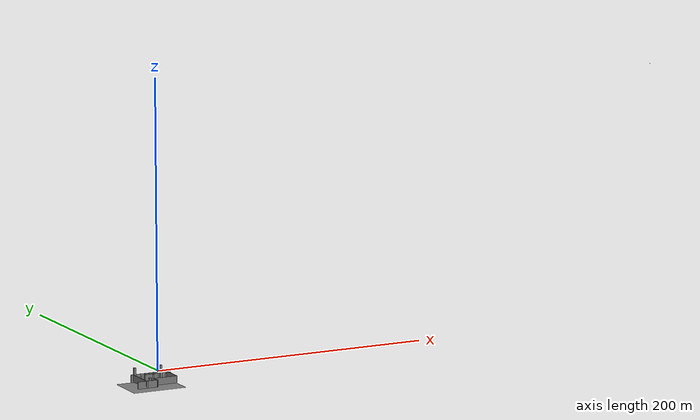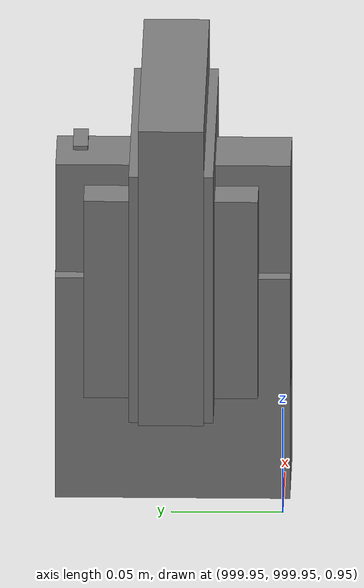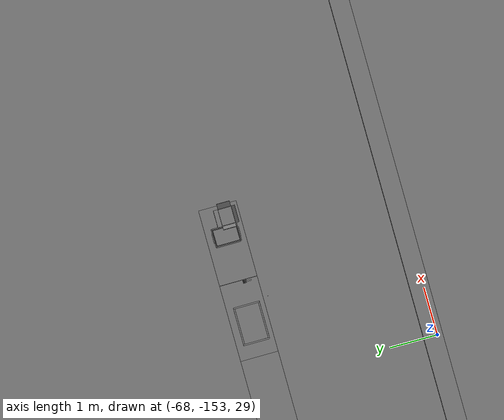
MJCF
<mujoco>
    <option gravity="0.000000000 0.000000000 -9.810000420" timestep="0.0049999999" integrator="implicitfast" density="1.225" viscosity="1.8000001e-05" noslip_iterations="10" iterations="100" sdf_iterations="50">
        <flag multiccd="disable"/>
    </option>
    <size memory="1000M"/>
    <compiler coordinate="local"/>
    <worldbody>
        <light cutoff="30" pos="0 1 1" dir="0 -1 -2"/>
        <light cutoff="30" pos="0 -1 1" dir="0 1 -2"/>
        <body pos="-64.866622925 -149.383972168 30.183746338" euler="89.999984741 89.999946594 0.000000000" name="openloong_gripper_2f85_fix_base_usda_bluebox_01">
            <geom contype="1" conaffinity="1" density="1000" type="box" material="" rgba="0.500000000 0.500000000 0.500000000 1.000000000" solimp="0.899999976 0.949999988 0.001000000" friction="1.000000000 0.005000000 0.000100000" solref="0.020000000 1.000000000" margin="0" condim="3" group="0" pos="0.276580811 0.187225342 0.000068665" quat="0.707106948 0.000077471 0.707106352 0.000077486" size="0.100000001 0.057999998 0.010000000" name="openloong_gripper_2f85_fix_base_usda_geom_8A14F075_F6AB_4E3F_A109_57A0D6590AAB"/>
            <geom contype="1" conaffinity="1" density="1000" type="box" material="" rgba="0.500000000 0.500000000 0.500000000 1.000000000" solimp="0.899999976 0.949999988 0.001000000" friction="1.000000000 0.005000000 0.000100000" solref="0.020000000 1.000000000" margin="0" condim="3" group="0" pos="0.000000000 0.002883911 0.000000000" quat="0.999999881 0.000000000 0.000000000 0.000000000" size="0.254000008 0.003000000 0.172000006" name="openloong_gripper_2f85_fix_base_usda_geom_42D75F8A_B5EA_409A_95F9_7E26F8D805B7"/>
            <geom contype="1" conaffinity="1" density="1000" type="box" material="" rgba="0.500000000 0.500000000 0.500000000 1.000000000" solimp="0.899999976 0.949999988 0.001000000" friction="1.000000000 0.005000000 0.000100000" solref="0.020000000 1.000000000" margin="0" condim="3" group="0" pos="0.000000000 0.124874115 0.173484802" quat="0.999796331 0.020176515 -0.000000015 0.000000030" size="0.259999990 0.119999997 0.007000000" name="openloong_gripper_2f85_fix_base_usda_geom_2AEDF4A9_1BFA_4F16_8797_42EB4DDF46B1"/>
            <geom contype="1" conaffinity="1" density="1000" type="box" material="" rgba="0.500000000 0.500000000 0.500000000 1.000000000" solimp="0.899999976 0.949999988 0.001000000" friction="1.000000000 0.005000000 0.000100000" solref="0.020000000 1.000000000" margin="0" condim="3" group="0" pos="0.000000000 0.124874115 -0.173469543" quat="0.999796331 -0.020176545 -0.000000015 0.000000000" size="0.259999990 0.119999997 0.007000000" name="openloong_gripper_2f85_fix_base_usda_geom_F8C9A6B7_D473_435A_9220_B29F27FEFF93"/>
            <geom contype="1" conaffinity="1" density="1000" type="box" material="" rgba="0.500000000 0.500000000 0.500000000 1.000000000" solimp="0.899999976 0.949999988 0.001000000" friction="1.000000000 0.005000000 0.000100000" solref="0.020000000 1.000000000" margin="0" condim="3" group="0" pos="0.000000000 0.214008331 0.188980103" quat="0.999912977 0.013176724 0.000000015 0.000000000" size="0.259999990 0.029999999 0.012500000" name="openloong_gripper_2f85_fix_base_usda_geom_DFF6628B_E001_4B51_8D58_E6C7C821521F"/>
            <geom contype="1" conaffinity="1" density="1000" type="box" material="" rgba="0.500000000 0.500000000 0.500000000 1.000000000" solimp="0.899999976 0.949999988 0.001000000" friction="1.000000000 0.005000000 0.000100000" solref="0.020000000 1.000000000" margin="0" condim="3" group="0" pos="-0.258361816 0.125289917 0.001876831" quat="0.702796936 -0.020792112 0.710783124 0.020769298" size="0.189999998 0.119999997 0.009000000" name="openloong_gripper_2f85_fix_base_usda_geom_B9E9B0CD_3BDA_48AE_80DA_5DF1950882D1"/>
            <geom contype="1" conaffinity="1" density="1000" type="box" material="" rgba="0.500000000 0.500000000 0.500000000 1.000000000" solimp="0.899999976 0.949999988 0.001000000" friction="1.000000000 0.005000000 0.000100000" solref="0.020000000 1.000000000" margin="0" condim="3" group="0" pos="0.000000000 0.214008331 -0.188980103" quat="0.999912977 -0.013176769 0.000000030 0.000000015" size="0.259999990 0.029999999 0.012500000" name="openloong_gripper_2f85_fix_base_usda_geom_30422736_A15F_4162_8ECE_8060F82D5953"/>
            <geom contype="1" conaffinity="1" density="1000" type="box" material="" rgba="0.500000000 0.500000000 0.500000000 1.000000000" solimp="0.899999976 0.949999988 0.001000000" friction="1.000000000 0.005000000 0.000100000" solref="0.020000000 1.000000000" margin="0" condim="3" group="0" pos="-0.276611328 0.187225342 0.000068665" quat="0.707106650 0.000077441 0.707106709 0.000077456" size="0.100000001 0.057999998 0.010000000" name="openloong_gripper_2f85_fix_base_usda_geom_EDD9F210_3862_4CB8_B729_7EB1D12CF4BC"/>
            <geom contype="1" conaffinity="1" density="1000" type="box" material="" rgba="0.500000000 0.500000000 0.500000000 1.000000000" solimp="0.899999976 0.949999988 0.001000000" friction="1.000000000 0.005000000 0.000100000" solref="0.020000000 1.000000000" margin="0" condim="3" group="0" pos="0.258331299 0.125289917 0.001876831" quat="0.702851415 0.018856421 0.710823774 -0.019329369" size="0.189999998 0.119999997 0.009000000" name="openloong_gripper_2f85_fix_base_usda_geom_8197EAAD_B587_4414_B0A6_7D0A6E124D32"/>
            <freejoint name="openloong_gripper_2f85_fix_base_usda_bluebox_01_joint"/>
            <site size="0.005000000 0.005000000 0.005000000" rgba="0.500000000 0.500000000 0.500000000 1.000000000" pos="0.000000000 0.000000000 0.000000000" quat="0.999961913 0.008726534 0.000000000 0.000000000" group="0" type="sphere" name="openloong_gripper_2f85_fix_base_usda_bluebox_01site"/>
        </body>
        <body pos="-64.496299744 -149.491867065 30.235729218" euler="0.000000000 0.000000000 89.999946594" name="openloong_gripper_2f85_fix_base_usda_cardboardbox_01">
            <geom contype="1" conaffinity="1" density="1000" type="box" material="" rgba="0.500000000 0.500000000 0.500000000 1.000000000" solimp="0.899999976 0.949999988 0.001000000" friction="1.000000000 0.005000000 0.000100000" solref="0.020000000 1.000000000" margin="0" condim="3" group="0" pos="-0.003166199 -0.004086494 0.005052090" quat="1.000000000 0.000000000 0.000000000 0.000000000" size="0.142499998 0.177500010 0.005000000" name="openloong_gripper_2f85_fix_base_usda_geom_F601F331_6776_4493_922A_2F271F714169"/>
            <geom contype="1" conaffinity="1" density="1000" type="box" material="" rgba="0.500000000 0.500000000 0.500000000 1.000000000" solimp="0.899999976 0.949999988 0.001000000" friction="1.000000000 0.005000000 0.000100000" solref="0.020000000 1.000000000" margin="0" condim="3" group="0" pos="-0.003166199 0.170316696 0.150570869" quat="1.000000000 0.000000000 0.000000000 0.000000000" size="0.142499998 0.005000000 0.149999991" name="openloong_gripper_2f85_fix_base_usda_geom_02C6696D_18D7_4AFA_90ED_EDEC53444B99"/>
            <geom contype="1" conaffinity="1" density="1000" type="box" material="" rgba="0.500000000 0.500000000 0.500000000 1.000000000" solimp="0.899999976 0.949999988 0.001000000" friction="1.000000000 0.005000000 0.000100000" solref="0.020000000 1.000000000" margin="0" condim="3" group="0" pos="-0.147399902 -0.005307198 0.150570869" quat="1.000000000 0.000000000 0.000000000 0.000000000" size="0.005000000 0.177500010 0.149999991" name="openloong_gripper_2f85_fix_base_usda_geom_B4C11489_1BBD_470B_9CBC_612623D5B5E6"/>
            <geom contype="1" conaffinity="1" density="1000" type="box" material="" rgba="0.500000000 0.500000000 0.500000000 1.000000000" solimp="0.899999976 0.949999988 0.001000000" friction="1.000000000 0.005000000 0.000100000" solref="0.020000000 1.000000000" margin="0" condim="3" group="0" pos="0.140275955 -0.005307198 0.150570869" quat="1.000000000 0.000000000 0.000000000 0.000000000" size="0.005000000 0.177500010 0.149999991" name="openloong_gripper_2f85_fix_base_usda_geom_E9592B36_BCF4_4EC7_9651_BD1B2B8A4AC6"/>
            <geom contype="1" conaffinity="1" density="1000" type="box" material="" rgba="0.500000000 0.500000000 0.500000000 1.000000000" solimp="0.899999976 0.949999988 0.001000000" friction="1.000000000 0.005000000 0.000100000" solref="0.020000000 1.000000000" margin="0" condim="3" group="0" pos="-0.003166199 -0.181550980 0.150570869" quat="1.000000000 0.000000000 0.000000000 0.000000000" size="0.142499998 0.005000000 0.149999991" name="openloong_gripper_2f85_fix_base_usda_geom_84CAC431_F03A_451D_871D_A7B35A107D9C"/>
            <freejoint name="openloong_gripper_2f85_fix_base_usda_cardboardbox_01_joint"/>
            <site size="0.005000000 0.005000000 0.005000000" rgba="0.500000000 0.500000000 0.500000000 1.000000000" pos="0.000000000 0.000000000 0.000000000" quat="0.999961913 0.008726535 0.000000000 0.000000000" group="0" type="sphere" name="openloong_gripper_2f85_fix_base_usda_site_79FFD89F_DF34_4DB8_9B26_9C7AD5BEC475"/>
            <body pos="0.139160156 -0.004048347 0.301930904" euler="-179.999954224 49.383502960 179.999954224" name="openloong_gripper_2f85_fix_base_usda_A1_006">
                <geom contype="1" conaffinity="1" density="1000" type="box" material="" rgba="0.500000000 0.500000000 0.500000000 1.000000000" solimp="0.899999976 0.949999988 0.001000000" friction="1.000000000 0.005000000 0.000100000" solref="0.020000000 1.000000000" margin="0" condim="3" group="0" pos="-0.071587563 0.000009537 0.001745224" quat="0.999999881 0.000000000 0.000000000 0.000000000" size="0.071249999 0.179999992 0.002500000" name="openloong_gripper_2f85_fix_base_usda_geom_174505AB_23B6_48F2_8AAD_15C0DB383DF7"/>
                <joint armature="0" stiffness="0.07" damping="0.0099999998" axis="0.000000 1.000000 0.000000" type="hinge" name="openloong_gripper_2f85_fix_base_usda_A1_006"/>
            </body>
            <body pos="-0.145902634 -0.004086494 0.301938057" euler="-180.000000000 -60.000011444 -180.000000000" name="openloong_gripper_2f85_fix_base_usda_A2_006">
                <geom contype="1" conaffinity="1" density="1000" type="box" material="" rgba="0.500000000 0.500000000 0.500000000 1.000000000" solimp="0.899999976 0.949999988 0.001000000" friction="1.000000000 0.005000000 0.000100000" solref="0.020000000 1.000000000" margin="0" condim="3" group="0" pos="0.071268082 0.000009537 0.002717972" quat="0.000002921 0.000000000 -0.000000030 0.999999881" size="0.071249999 0.179999992 0.002500000" name="openloong_gripper_2f85_fix_base_usda_geom_EDF6B94E_634E_453F_9359_B2D7D56E5585"/>
                <joint armature="0" stiffness="0.07" damping="0.0099999998" axis="0.000000 1.000000 0.000000" type="hinge" name="openloong_gripper_2f85_fix_base_usda_A2_006"/>
            </body>
            <body pos="-0.003385544 0.175991058 0.301930904" euler="-125.858116150 -0.000004561 0.000002331" name="openloong_gripper_2f85_fix_base_usda_B2_006">
                <geom contype="1" conaffinity="1" density="1000" type="box" material="" rgba="0.500000000 0.500000000 0.500000000 1.000000000" solimp="0.899999976 0.949999988 0.001000000" friction="1.000000000 0.005000000 0.000100000" solref="0.020000000 1.000000000" margin="0" condim="3" group="0" pos="0.000009537 -0.070939064 -0.002470016" quat="0.999614120 0.027776197 -0.000000015 0.000000030" size="0.137500003 0.064999998 0.005000000" name="openloong_gripper_2f85_fix_base_usda_geom_0FD2E017_50DE_4467_9311_C6CBAF0A0D7A"/>
                <joint armature="0" stiffness="0.07" damping="0.0099999998" axis="1.000000 0.000000 0.000000" type="hinge" name="openloong_gripper_2f85_fix_base_usda_B2_006"/>
            </body>
            <body pos="-0.003385544 -0.184140205 0.301938057" euler="147.805557251 0.000000000 0.000000000" name="openloong_gripper_2f85_fix_base_usda_B1_006">
                <geom contype="1" conaffinity="1" density="1000" type="box" material="" rgba="0.500000000 0.500000000 0.500000000 1.000000000" solimp="0.899999976 0.949999988 0.001000000" friction="1.000000000 0.005000000 0.000100000" solref="0.020000000 1.000000000" margin="0" condim="3" group="0" pos="-0.000028610 0.070202351 -0.002703667" quat="0.999614179 -0.027776167 0.000000000 0.000000000" size="0.137500003 0.064999998 0.005000000" name="openloong_gripper_2f85_fix_base_usda_geom_4C489981_DAAE_4246_B9FE_932FB9EC9E90"/>
                <joint armature="0" stiffness="0.07" damping="0.0099999998" axis="1.000000 0.000000 0.000000" type="hinge" name="openloong_gripper_2f85_fix_base_usda_B1_006"/>
            </body>
        </body>
        <body pos="-65.882858276 -149.481979370 30.229999542" euler="-64.487716675 0.000000000 0.000000000" name="openloong_gripper_2f85_fix_base_usda_Barcode">
            <geom contype="1" conaffinity="1" density="1000" type="box" material="" rgba="0.500000000 0.500000000 0.500000000 1.000000000" solimp="0.899999976 0.949999988 0.001000000" friction="1.000000000 0.005000000 0.000100000" solref="0.020000000 1.000000000" margin="0" condim="3" group="0" pos="0.000000000 0.013038635 0.001419067" quat="0.000000000 0.000000000 0.000000000 1.000000119" size="0.034000002 0.010000000 0.017999999" name="openloong_gripper_2f85_fix_base_usda_geom_251FE4D2_1FC0_47CE_A51F_CD2B171CEE35"/>
            <geom contype="1" conaffinity="1" density="1000" type="box" material="" rgba="0.500000000 0.500000000 0.500000000 1.000000000" solimp="0.899999976 0.949999988 0.001000000" friction="1.000000000 0.005000000 0.000100000" solref="0.020000000 1.000000000" margin="0" condim="3" group="0" pos="0.000000000 -0.035301208 -0.007095337" quat="0.000000000 0.000000000 -0.043619365 0.999048233" size="0.028999999 0.010000000 0.020000000" name="openloong_gripper_2f85_fix_base_usda_geom_864777B1_A077_4184_B528_6E6120D7030E"/>
            <geom contype="1" conaffinity="1" density="1000" type="box" material="" rgba="0.500000000 0.500000000 0.500000000 1.000000000" solimp="0.899999976 0.949999988 0.001000000" friction="1.000000000 0.005000000 0.000100000" solref="0.020000000 1.000000000" margin="0" condim="3" group="0" pos="0.000000000 -0.043411255 -0.011749268" quat="0.922262907 0.386563420 0.000000000 0.000000000" size="0.026000001 0.010000000 0.020000000" name="openloong_gripper_2f85_fix_base_usda_geom_A1A8442C_C21E_4B80_9EEA_752B1101821D"/>
            <geom contype="1" conaffinity="1" density="1000" type="box" material="" rgba="0.500000000 0.500000000 0.500000000 1.000000000" solimp="0.899999976 0.949999988 0.001000000" friction="1.000000000 0.005000000 0.000100000" solref="0.020000000 1.000000000" margin="0" condim="3" group="0" pos="0.000000000 -0.016967773 -0.031860352" quat="0.000000000 0.000000000 0.000000000 1.000000119" size="0.008000000 0.010000000 0.013000000" name="openloong_gripper_2f85_fix_base_usda_geom_C0AA16A1_3114_41B2_8D3D_952FD0A08737"/>
            <geom contype="1" conaffinity="1" density="1000" type="box" material="" rgba="0.500000000 0.500000000 0.500000000 1.000000000" solimp="0.899999976 0.949999988 0.001000000" friction="1.000000000 0.005000000 0.000100000" solref="0.020000000 1.000000000" margin="0" condim="3" group="0" pos="0.000000000 -0.001869202 0.000312805" quat="0.953716993 0.300705761 0.000000000 0.000000000" size="0.032000002 0.010000000 0.018999999" name="openloong_gripper_2f85_fix_base_usda_geom_39747500_28A8_4058_BA4E_3F14742A6CC2"/>
            <geom contype="1" conaffinity="1" density="1000" type="box" material="" rgba="0.500000000 0.500000000 0.500000000 1.000000000" solimp="0.899999976 0.949999988 0.001000000" friction="1.000000000 0.005000000 0.000100000" solref="0.020000000 1.000000000" margin="0" condim="3" group="0" pos="0.000000000 -0.019531250 -0.003173828" quat="0.953716993 0.300705761 0.000000000 0.000000000" size="0.030999999 0.010000000 0.020000000" name="openloong_gripper_2f85_fix_base_usda_geom_CDE26FC9_3BA3_4A94_B700_9D211DDA0841"/>
            <geom contype="1" conaffinity="1" density="1000" type="box" material="" rgba="0.500000000 0.500000000 0.500000000 1.000000000" solimp="0.899999976 0.949999988 0.001000000" friction="1.000000000 0.005000000 0.000100000" solref="0.020000000 1.000000000" margin="0" condim="3" group="0" pos="0.000000000 -0.035301208 -0.007095337" quat="0.953716993 0.300705761 0.000000000 0.000000000" size="0.028999999 0.010000000 0.020000000" name="openloong_gripper_2f85_fix_base_usda_geom_70EAE295_3FA9_4E60_AFFE_1C4129E9B964"/>
            <geom contype="1" conaffinity="1" density="1000" type="box" material="" rgba="0.500000000 0.500000000 0.500000000 1.000000000" solimp="0.899999976 0.949999988 0.001000000" friction="1.000000000 0.005000000 0.000100000" solref="0.020000000 1.000000000" margin="0" condim="3" group="0" pos="0.000000000 -0.042617798 -0.071121216" quat="0.000000000 0.000000000 0.000000000 1.000000119" size="0.013000000 0.021000000 0.059999999" name="openloong_gripper_2f85_fix_base_usda_geom_CB87073B_BDEB_45EE_8F19_812B81DC75A8"/>
            <freejoint name="openloong_gripper_2f85_fix_base_usda_Barcode_joint"/>
            <site size="0.005000000 0.005000000 0.005000000" rgba="0.500000000 0.500000000 0.500000000 1.000000000" pos="0.000000000 0.000000000 0.000000000" quat="1.000000000 0.000000000 0.000000000 0.000000000" group="0" type="sphere" name="openloong_gripper_2f85_fix_base_usda_Barcode_site"/>
        </body>
        <body pos="-66.745018005 -149.392349243 30.184000015" euler="0.000000000 0.000000000 89.999946594" name="[22333740026501]_Basket_01">
            <geom contype="1" conaffinity="1" density="1000" type="box" material="" rgba="0.500000000 0.500000000 0.500000000 1.000000000" solimp="0.899999976 0.949999988 0.001000000" friction="1.000000000 0.005000000 0.000100000" solref="0.020000000 1.000000000" margin="0" condim="3" group="0" pos="-0.052425385 0.389207840 0.089787483" quat="0.707107008 0.000000000 0.000000000 0.707106411" size="0.014249999 0.014249999 0.059999999" name="[22333740026501]_geom_BC8C10AD_E0C4_4455_82D4_F790EF22EBEE"/>
            <geom contype="1" conaffinity="1" density="1000" type="box" material="" rgba="0.500000000 0.500000000 0.500000000 1.000000000" solimp="0.899999976 0.949999988 0.001000000" friction="1.000000000 0.005000000 0.000100000" solref="0.020000000 1.000000000" margin="0" condim="3" group="0" pos="0.264015198 -0.133043289 0.089787483" quat="0.707107008 0.000000000 0.000000000 0.707106411" size="0.014249999 0.014249999 0.059999999" name="[22333740026501]_geom_90BEB09A_5A2C_411C_A1E5_1BB14E203296"/>
            <geom contype="1" conaffinity="1" density="1000" type="box" material="" rgba="0.500000000 0.500000000 0.500000000 1.000000000" solimp="0.899999976 0.949999988 0.001000000" friction="1.000000000 0.005000000 0.000100000" solref="0.020000000 1.000000000" margin="0" condim="3" group="0" pos="-0.264015198 -0.265548706 0.089793205" quat="0.707107008 0.000000000 0.000000000 0.707106411" size="0.014249999 0.014249999 0.059999999" name="[22333740026501]_geom_7B4B9EA8_9D15_47E7_966A_3C8371486F36"/>
            <geom contype="1" conaffinity="1" density="1000" type="box" material="" rgba="0.500000000 0.500000000 0.500000000 1.000000000" solimp="0.899999976 0.949999988 0.001000000" friction="1.000000000 0.005000000 0.000100000" solref="0.020000000 1.000000000" margin="0" condim="3" group="0" pos="-0.160263062 -0.389322281 0.089793205" quat="0.707107008 0.000000000 0.000000000 0.707106411" size="0.014249999 0.014249999 0.059999999" name="[22333740026501]_geom_57CCFAAE_9B72_4518_B9F0_54C980C014C4"/>
            <geom contype="1" conaffinity="1" density="1000" type="box" material="" rgba="0.500000000 0.500000000 0.500000000 1.000000000" solimp="0.899999976 0.949999988 0.001000000" friction="1.000000000 0.005000000 0.000100000" solref="0.020000000 1.000000000" margin="0" condim="3" group="0" pos="0.162265778 -0.389322281 0.089787483" quat="0.707107008 0.000000000 0.000000000 0.707106411" size="0.014249999 0.014249999 0.059999999" name="[22333740026501]_geom_A0C078DD_FC4F_4916_BE7D_16E36A544D4C"/>
            <geom contype="1" conaffinity="1" density="1000" type="box" material="" rgba="0.500000000 0.500000000 0.500000000 1.000000000" solimp="0.899999976 0.949999988 0.001000000" friction="1.000000000 0.005000000 0.000100000" solref="0.020000000 1.000000000" margin="0" condim="3" group="0" pos="0.264015198 0.389207840 0.089787483" quat="0.707107008 0.000000000 0.000000000 0.707106411" size="0.014249999 0.014249999 0.059999999" name="[22333740026501]_geom_2CBFE2BB_86A5_467C_92BE_3AE1C9C331AF"/>
            <geom contype="1" conaffinity="1" density="1000" type="box" material="" rgba="0.500000000 0.500000000 0.500000000 1.000000000" solimp="0.899999976 0.949999988 0.001000000" friction="1.000000000 0.005000000 0.000100000" solref="0.020000000 1.000000000" margin="0" condim="3" group="0" pos="-0.264015198 -0.133043289 0.089793205" quat="0.707107008 0.000000000 0.000000000 0.707106411" size="0.014249999 0.014249999 0.059999999" name="[22333740026501]_geom_8D94CD28_6FB7_439C_ACE7_8111C6FC9342"/>
            <geom contype="1" conaffinity="1" density="1000" type="box" material="" rgba="0.500000000 0.500000000 0.500000000 1.000000000" solimp="0.899999976 0.949999988 0.001000000" friction="1.000000000 0.005000000 0.000100000" solref="0.020000000 1.000000000" margin="0" condim="3" group="0" pos="-0.264026642 0.269256592 0.089793205" quat="0.707107008 0.000000000 0.000000000 0.707106411" size="0.014249999 0.014249999 0.059999999" name="[22333740026501]_geom_91CB71C3_8FEE_42A3_B459_BD42F5DC95B0"/>
            <geom contype="1" conaffinity="1" density="1000" type="box" material="" rgba="0.500000000 0.500000000 0.500000000 1.000000000" solimp="0.899999976 0.949999988 0.001000000" friction="1.000000000 0.005000000 0.000100000" solref="0.020000000 1.000000000" margin="0" condim="3" group="0" pos="0.054462433 0.389207840 0.089787483" quat="0.707107008 0.000000000 0.000000000 0.707106411" size="0.014249999 0.014249999 0.059999999" name="[22333740026501]_geom_D4644016_5139_4CDC_B4CA_B30BF1B6AF60"/>
            <geom contype="1" conaffinity="1" density="1000" type="box" material="" rgba="0.500000000 0.500000000 0.500000000 1.000000000" solimp="0.899999976 0.949999988 0.001000000" friction="1.000000000 0.005000000 0.000100000" solref="0.020000000 1.000000000" margin="0" condim="3" group="0" pos="0.054462433 -0.389322281 0.089787483" quat="0.707107008 0.000000000 0.000000000 0.707106411" size="0.014249999 0.014249999 0.059999999" name="[22333740026501]_geom_98BDA36A_2C7C_4DCB_A842_AF9AFDA571BB"/>
            <geom contype="1" conaffinity="1" density="1000" type="box" material="" rgba="0.500000000 0.500000000 0.500000000 1.000000000" solimp="0.899999976 0.949999988 0.001000000" friction="1.000000000 0.005000000 0.000100000" solref="0.020000000 1.000000000" margin="0" condim="3" group="0" pos="0.264015198 0.269256592 0.089793205" quat="0.707107008 0.000000000 0.000000000 0.707106411" size="0.014249999 0.014249999 0.059999999" name="[22333740026501]_geom_F7406650_277B_4061_A7E2_7EE3D40549B5"/>
            <geom contype="1" conaffinity="1" density="1000" type="box" material="" rgba="0.500000000 0.500000000 0.500000000 1.000000000" solimp="0.899999976 0.949999988 0.001000000" friction="1.000000000 0.005000000 0.000100000" solref="0.020000000 1.000000000" margin="0" condim="3" group="0" pos="0.264015198 -0.389322281 0.089787483" quat="0.707107008 0.000000000 0.000000000 0.707106411" size="0.014249999 0.014249999 0.059999999" name="[22333740026501]_geom_FB18710C_C042_49E5_87B4_5C55BB9DEA0C"/>
            <geom contype="1" conaffinity="1" density="1000" type="box" material="" rgba="0.500000000 0.500000000 0.500000000 1.000000000" solimp="0.899999976 0.949999988 0.001000000" friction="1.000000000 0.005000000 0.000100000" solref="0.020000000 1.000000000" margin="0" condim="3" group="0" pos="0.000000000 0.000000000 0.015998840" quat="0.707107008 0.000000000 0.000000000 0.707106411" size="0.403499991 0.279000014 0.015750000" name="[22333740026501]_geom_F3FC0086_DE2F_4A90_AA13_F5710E9DFB81"/>
            <geom contype="1" conaffinity="1" density="1000" type="box" material="" rgba="0.500000000 0.500000000 0.500000000 1.000000000" solimp="0.899999976 0.949999988 0.001000000" friction="1.000000000 0.005000000 0.000100000" solref="0.020000000 1.000000000" margin="0" condim="3" group="0" pos="0.000000000 -0.389476776 0.163619041" quat="0.707107008 0.000000000 0.000000000 0.707106411" size="0.015000000 0.277500004 0.015750000" name="[22333740026501]_geom_EDB62CF1_7F95_43E9_8DB7_BCABA6028E0C"/>
            <geom contype="1" conaffinity="1" density="1000" type="box" material="" rgba="0.500000000 0.500000000 0.500000000 1.000000000" solimp="0.899999976 0.949999988 0.001000000" friction="1.000000000 0.005000000 0.000100000" solref="0.020000000 1.000000000" margin="0" condim="3" group="0" pos="0.162265778 0.389207840 0.089787483" quat="0.707107008 0.000000000 0.000000000 0.707106411" size="0.014249999 0.014249999 0.059999999" name="[22333740026501]_geom_A639471F_71D3_4BEB_972D_3A6E5B347955"/>
            <geom contype="1" conaffinity="1" density="1000" type="box" material="" rgba="0.500000000 0.500000000 0.500000000 1.000000000" solimp="0.899999976 0.949999988 0.001000000" friction="1.000000000 0.005000000 0.000100000" solref="0.020000000 1.000000000" margin="0" condim="3" group="0" pos="0.000000000 0.389471054 0.163619041" quat="0.707107008 0.000000000 0.000000000 0.707106411" size="0.015000000 0.277500004 0.015750000" name="[22333740026501]_geom_BA92F0E4_43E5_4CC7_9A92_AECB097A2BA1"/>
            <geom contype="1" conaffinity="1" density="1000" type="box" material="" rgba="0.500000000 0.500000000 0.500000000 1.000000000" solimp="0.899999976 0.949999988 0.001000000" friction="1.000000000 0.005000000 0.000100000" solref="0.020000000 1.000000000" margin="0" condim="3" group="0" pos="-0.263511658 0.000000000 0.163619041" quat="0.707107008 0.000000000 0.000000000 0.707106411" size="0.403499991 0.015000000 0.015750000" name="[22333740026501]_geom_6CC28F45_4990_4B84_9213_4DD4AA0AD4D0"/>
            <geom contype="1" conaffinity="1" density="1000" type="box" material="" rgba="0.500000000 0.500000000 0.500000000 1.000000000" solimp="0.899999976 0.949999988 0.001000000" friction="1.000000000 0.005000000 0.000100000" solref="0.020000000 1.000000000" margin="0" condim="3" group="0" pos="-0.264015198 0.141334534 0.089793205" quat="0.707107008 0.000000000 0.000000000 0.707106411" size="0.014249999 0.014249999 0.059999999" name="[22333740026501]_geom_9C8B1F3C_A20C_4962_B8D1_A6122562DBCC"/>
            <geom contype="1" conaffinity="1" density="1000" type="box" material="" rgba="0.500000000 0.500000000 0.500000000 1.000000000" solimp="0.899999976 0.949999988 0.001000000" friction="1.000000000 0.005000000 0.000100000" solref="0.020000000 1.000000000" margin="0" condim="3" group="0" pos="0.264015198 -0.265548706 0.089787483" quat="0.707107008 0.000000000 0.000000000 0.707106411" size="0.014249999 0.014249999 0.059999999" name="[22333740026501]_geom_4B08960D_1B24_48EF_A7EF_1CC958C02929"/>
            <geom contype="1" conaffinity="1" density="1000" type="box" material="" rgba="0.500000000 0.500000000 0.500000000 1.000000000" solimp="0.899999976 0.949999988 0.001000000" friction="1.000000000 0.005000000 0.000100000" solref="0.020000000 1.000000000" margin="0" condim="3" group="0" pos="-0.160263062 0.389207840 0.089787483" quat="0.707107008 0.000000000 0.000000000 0.707106411" size="0.014249999 0.014249999 0.059999999" name="[22333740026501]_geom_56915A53_6656_457B_BFB7_5F18DC6F1DB3"/>
            <geom contype="1" conaffinity="1" density="1000" type="box" material="" rgba="0.500000000 0.500000000 0.500000000 1.000000000" solimp="0.899999976 0.949999988 0.001000000" friction="1.000000000 0.005000000 0.000100000" solref="0.020000000 1.000000000" margin="0" condim="3" group="0" pos="-0.052425385 -0.389322281 0.089787483" quat="0.707107008 0.000000000 0.000000000 0.707106411" size="0.014249999 0.014249999 0.059999999" name="[22333740026501]_geom_86B44F12_FFF0_467C_961E_D08511B9979D"/>
            <geom contype="1" conaffinity="1" density="1000" type="box" material="" rgba="0.500000000 0.500000000 0.500000000 1.000000000" solimp="0.899999976 0.949999988 0.001000000" friction="1.000000000 0.005000000 0.000100000" solref="0.020000000 1.000000000" margin="0" condim="3" group="0" pos="-0.264026642 -0.389322281 0.089793205" quat="0.707107008 0.000000000 0.000000000 0.707106411" size="0.014249999 0.014249999 0.059999999" name="[22333740026501]_geom_0A6CF5B2_E4E9_4490_8AAD_8351527C324D"/>
            <geom contype="1" conaffinity="1" density="1000" type="box" material="" rgba="0.500000000 0.500000000 0.500000000 1.000000000" solimp="0.899999976 0.949999988 0.001000000" friction="1.000000000 0.005000000 0.000100000" solref="0.020000000 1.000000000" margin="0" condim="3" group="0" pos="0.264015198 0.141334534 0.089787483" quat="0.707107008 0.000000000 0.000000000 0.707106411" size="0.014249999 0.014249999 0.059999999" name="[22333740026501]_geom_CBFA7967_3FBF_42EF_80EC_890CD708B4C3"/>
            <geom contype="1" conaffinity="1" density="1000" type="box" material="" rgba="0.500000000 0.500000000 0.500000000 1.000000000" solimp="0.899999976 0.949999988 0.001000000" friction="1.000000000 0.005000000 0.000100000" solref="0.020000000 1.000000000" margin="0" condim="3" group="0" pos="-0.264015198 0.389207840 0.089793205" quat="0.707107008 0.000000000 0.000000000 0.707106411" size="0.014249999 0.014249999 0.059999999" name="[22333740026501]_geom_30932D8C_4796_45F6_BC18_3A3630F3A0A8"/>
            <geom contype="1" conaffinity="1" density="1000" type="box" material="" rgba="0.500000000 0.500000000 0.500000000 1.000000000" solimp="0.899999976 0.949999988 0.001000000" friction="1.000000000 0.005000000 0.000100000" solref="0.020000000 1.000000000" margin="0" condim="3" group="0" pos="0.264015198 0.004480362 0.089787483" quat="0.707107008 0.000000000 0.000000000 0.707106411" size="0.014249999 0.014249999 0.059999999" name="[22333740026501]_geom_2292FDCA_B8F7_44EC_9AFD_3BCBE1CAD803"/>
            <geom contype="1" conaffinity="1" density="1000" type="box" material="" rgba="0.500000000 0.500000000 0.500000000 1.000000000" solimp="0.899999976 0.949999988 0.001000000" friction="1.000000000 0.005000000 0.000100000" solref="0.020000000 1.000000000" margin="0" condim="3" group="0" pos="0.263694763 -0.000011444 0.163619041" quat="0.707107008 0.000000000 0.000000000 0.707106411" size="0.403499991 0.015000000 0.015750000" name="[22333740026501]_geom_1ACA75A5_D931_447B_ACC2_12F187188598"/>
            <geom contype="1" conaffinity="1" density="1000" type="box" material="" rgba="0.500000000 0.500000000 0.500000000 1.000000000" solimp="0.899999976 0.949999988 0.001000000" friction="1.000000000 0.005000000 0.000100000" solref="0.020000000 1.000000000" margin="0" condim="3" group="0" pos="-0.264015198 0.004480362 0.089793205" quat="0.707107008 0.000000000 0.000000000 0.707106411" size="0.014249999 0.014249999 0.059999999" name="[22333740026501]_geom_A558ABA1_E538_499F_831B_5FEE87A9189F"/>
            <freejoint name="[22333740026501]_joint_1C13812B_8484_4A96_853C_44FB536D1290"/>
        </body>
        <body pos="0.000000000 0.000000000 0.000000000" euler="0.000000000 0.000000000 0.000000000" name="Static Objects_Static Objects">
            <geom contype="1" conaffinity="1" density="1000" type="box" material="" rgba="0.500000000 0.500000000 0.500000000 1.000000000" solimp="0.899999976 0.949999988 0.001000000" friction="1.000000000 0.005000000 0.000100000" solref="0.020000000 1.000000000" margin="0" condim="3" group="0" pos="-67.544113159 -149.365814209 29.727830887" quat="0.500000417 0.499999970 0.499999553 0.499999970" size="0.381000012 0.319999993 0.041000001" name="Static Objects_geom_5217D8A5_FBFA_4FC8_8931_3B8890F239AD"/>
            <geom contype="1" conaffinity="1" density="1000" type="box" material="" rgba="0.500000000 0.500000000 0.500000000 1.000000000" solimp="0.899999976 0.949999988 0.001000000" friction="1.000000000 0.005000000 0.000100000" solref="0.020000000 1.000000000" margin="0" condim="3" group="0" pos="-68.239501953 -149.365814209 30.086868286" quat="0.500000417 0.499999970 0.499999553 0.499999970" size="0.370999992 0.039500002 0.745000005" name="Static Objects_geom_15C1E37D_B5FB_4CC2_B420_F4A2DFEA7795"/>
            <geom contype="1" conaffinity="1" density="1000" type="box" material="" rgba="0.500000000 0.500000000 0.500000000 1.000000000" solimp="0.899999976 0.949999988 0.001000000" friction="1.000000000 0.005000000 0.000100000" solref="0.020000000 1.000000000" margin="0" condim="3" group="0" pos="-68.239501953 -149.365814209 30.147235870" quat="0.500000417 0.499999970 0.499999553 0.499999970" size="0.400000006 0.022000000 0.800000012" name="Static Objects_geom_33956E7C_6177_4617_8516_325A34B10B6B"/>
            <geom contype="1" conaffinity="1" density="1000" type="box" material="" rgba="0.500000000 0.500000000 0.500000000 1.000000000" solimp="0.899999976 0.949999988 0.001000000" friction="1.000000000 0.005000000 0.000100000" solref="0.020000000 1.000000000" margin="0" condim="3" group="0" pos="-68.934890747 -149.365814209 29.727830887" quat="0.500000417 0.499999970 0.499999553 0.499999970" size="0.381000012 0.319999993 0.041000001" name="Static Objects_geom_4690D1BB_13EF_41E3_9D95_F5BB1EC2529C"/>
            <geom contype="1" conaffinity="1" density="1000" type="box" material="" rgba="0.500000000 0.500000000 0.500000000 1.000000000" solimp="0.899999976 0.949999988 0.001000000" friction="1.000000000 0.005000000 0.000100000" solref="0.020000000 1.000000000" margin="0" condim="3" group="0" pos="-68.239501953 -149.365814209 29.561563492" quat="0.500000417 0.499999970 0.499999553 0.499999970" size="0.020000000 0.022000000 0.660000026" name="Static Objects_geom_125A3052_C4A8_4F10_BC0B_379A27082CA3"/>
            <geom contype="1" conaffinity="1" density="1000" type="box" material="" rgba="0.500000000 0.500000000 0.500000000 1.000000000" solimp="0.899999976 0.949999988 0.001000000" friction="1.000000000 0.005000000 0.000100000" solref="0.020000000 1.000000000" margin="0" condim="3" group="0" pos="-65.945671082 -149.365814209 29.727830887" quat="0.500000417 0.499999970 0.499999553 0.499999970" size="0.381000012 0.319999993 0.041000001" name="Static Objects_geom_DACBFA3F_ADC4_4981_ADBA_960636F6A8F4"/>
            <geom contype="1" conaffinity="1" density="1000" type="box" material="" rgba="0.500000000 0.500000000 0.500000000 1.000000000" solimp="0.899999976 0.949999988 0.001000000" friction="1.000000000 0.005000000 0.000100000" solref="0.020000000 1.000000000" margin="0" condim="3" group="0" pos="-66.641059875 -149.365814209 30.086868286" quat="0.500000417 0.499999970 0.499999553 0.499999970" size="0.370999992 0.039500002 0.745000005" name="Static Objects_geom_84C0A072_BCD8_4287_9E43_E559456EEE4A"/>
            <geom contype="1" conaffinity="1" density="1000" type="box" material="" rgba="0.500000000 0.500000000 0.500000000 1.000000000" solimp="0.899999976 0.949999988 0.001000000" friction="1.000000000 0.005000000 0.000100000" solref="0.020000000 1.000000000" margin="0" condim="3" group="0" pos="-66.641059875 -149.365814209 30.147235870" quat="0.500000417 0.499999970 0.499999553 0.499999970" size="0.400000006 0.022000000 0.800000012" name="Static Objects_geom_9CC681F5_DF15_4906_AF3A_947A15D9393F"/>
            <geom contype="1" conaffinity="1" density="1000" type="box" material="" rgba="0.500000000 0.500000000 0.500000000 1.000000000" solimp="0.899999976 0.949999988 0.001000000" friction="1.000000000 0.005000000 0.000100000" solref="0.020000000 1.000000000" margin="0" condim="3" group="0" pos="-67.336448669 -149.365814209 29.727830887" quat="0.500000417 0.499999970 0.499999553 0.499999970" size="0.381000012 0.319999993 0.041000001" name="Static Objects_geom_8ED1ECEF_2081_4AA0_A278_343575F81CB7"/>
            <geom contype="1" conaffinity="1" density="1000" type="box" material="" rgba="0.500000000 0.500000000 0.500000000 1.000000000" solimp="0.899999976 0.949999988 0.001000000" friction="1.000000000 0.005000000 0.000100000" solref="0.020000000 1.000000000" margin="0" condim="3" group="0" pos="-66.641059875 -149.365814209 29.561563492" quat="0.500000417 0.499999970 0.499999553 0.499999970" size="0.020000000 0.022000000 0.660000026" name="Static Objects_geom_3D770CEE_F551_431E_B412_7FBB51970C52"/>
            <geom contype="1" conaffinity="1" density="1000" type="box" material="" rgba="0.500000000 0.500000000 0.500000000 1.000000000" solimp="0.899999976 0.949999988 0.001000000" friction="1.000000000 0.005000000 0.000100000" solref="0.020000000 1.000000000" margin="0" condim="3" group="0" pos="-64.338577271 -149.365814209 29.727830887" quat="0.500000417 0.499999970 0.499999553 0.499999970" size="0.381000012 0.319999993 0.041000001" name="Static Objects_geom_724D437B_5204_43C8_B96E_A3C145D76B89"/>
            <geom contype="1" conaffinity="1" density="1000" type="box" material="" rgba="0.500000000 0.500000000 0.500000000 1.000000000" solimp="0.899999976 0.949999988 0.001000000" friction="1.000000000 0.005000000 0.000100000" solref="0.020000000 1.000000000" margin="0" condim="3" group="0" pos="-65.033966064 -149.365814209 30.086868286" quat="0.500000417 0.499999970 0.499999553 0.499999970" size="0.370999992 0.039500002 0.745000005" name="Static Objects_geom_F7DD5B28_542F_4FA6_A426_D8E5619AF838"/>
            <geom contype="1" conaffinity="1" density="1000" type="box" material="" rgba="0.500000000 0.500000000 0.500000000 1.000000000" solimp="0.899999976 0.949999988 0.001000000" friction="1.000000000 0.005000000 0.000100000" solref="0.020000000 1.000000000" margin="0" condim="3" group="0" pos="-65.033966064 -149.365814209 30.147235870" quat="0.500000417 0.499999970 0.499999553 0.499999970" size="0.400000006 0.022000000 0.800000012" name="Static Objects_geom_B89BE421_7ABC_4581_AE5A_2170315B0E1C"/>
            <geom contype="1" conaffinity="1" density="1000" type="box" material="" rgba="0.500000000 0.500000000 0.500000000 1.000000000" solimp="0.899999976 0.949999988 0.001000000" friction="1.000000000 0.005000000 0.000100000" solref="0.020000000 1.000000000" margin="0" condim="3" group="0" pos="-65.729354858 -149.365814209 29.727830887" quat="0.500000417 0.499999970 0.499999553 0.499999970" size="0.381000012 0.319999993 0.041000001" name="Static Objects_geom_0176B305_01CE_4F71_9C5F_363EC3E4975A"/>
            <geom contype="1" conaffinity="1" density="1000" type="box" material="" rgba="0.500000000 0.500000000 0.500000000 1.000000000" solimp="0.899999976 0.949999988 0.001000000" friction="1.000000000 0.005000000 0.000100000" solref="0.020000000 1.000000000" margin="0" condim="3" group="0" pos="-65.033966064 -149.365814209 29.561563492" quat="0.500000417 0.499999970 0.499999553 0.499999970" size="0.020000000 0.022000000 0.660000026" name="Static Objects_geom_429AE842_2805_4374_BBA5_167A5B6C66C1"/>
            <geom contype="1" conaffinity="1" density="1000" type="box" material="" rgba="0.500000000 0.500000000 0.500000000 1.000000000" solimp="0.899999976 0.949999988 0.001000000" friction="1.000000000 0.005000000 0.000100000" solref="0.020000000 1.000000000" margin="0" condim="3" group="0" pos="-61.754566193 -137.853729248 33.906845093" quat="0.707107067 0.000000000 0.000000000 0.707106471" size="0.759999990 0.759999990 4.500000000" name="Static Objects_geom_7A5D56B0_259C_477D_AA05_6398C624EB99"/>
            <geom contype="1" conaffinity="1" density="1000" type="box" material="" rgba="0.500000000 0.500000000 0.500000000 1.000000000" solimp="0.899999976 0.949999988 0.001000000" friction="1.000000000 0.005000000 0.000100000" solref="0.020000000 1.000000000" margin="0" condim="3" group="0" pos="-57.511135101 -144.927108765 31.707921982" quat="1.000000000 0.000000000 0.000000000 0.000000000" size="0.200000003 8.000000000 2.299999952" name="Static Objects_geom_C7BEF276_A686_4BF1_9458_27BEAF5DF5D7"/>
            <geom contype="1" conaffinity="1" density="1000" type="box" material="" rgba="0.500000000 0.500000000 0.500000000 1.000000000" solimp="0.899999976 0.949999988 0.001000000" friction="1.000000000 0.005000000 0.000100000" solref="0.020000000 1.000000000" margin="0" condim="3" group="0" pos="-80.517646790 -157.574050903 31.688196182" quat="0.707107067 0.000000000 0.000000000 0.707106471" size="0.600000024 0.600000024 2.299999952" name="Static Objects_geom_0A1DC5E1_EF53_4D6D_8C4D_E030D044E1E6"/>
            <geom contype="1" conaffinity="1" density="1000" type="box" material="" rgba="0.500000000 0.500000000 0.500000000 1.000000000" solimp="0.899999976 0.949999988 0.001000000" friction="1.000000000 0.005000000 0.000100000" solref="0.020000000 1.000000000" margin="0" condim="3" group="0" pos="-80.711044312 -147.414932251 31.666158676" quat="1.000000000 0.000000000 0.000000000 0.000000000" size="0.200000003 10.000000000 2.299999952" name="Static Objects_geom_B9F9FD36_3F33_45E1_A1DC_03946033AF98"/>
            <geom contype="1" conaffinity="1" density="1000" type="box" material="" rgba="0.500000000 0.500000000 0.500000000 1.000000000" solimp="0.899999976 0.949999988 0.001000000" friction="1.000000000 0.005000000 0.000100000" solref="0.020000000 1.000000000" margin="0" condim="3" group="0" pos="-57.687217712 -137.434692383 31.688196182" quat="0.707107067 0.000000000 0.000000000 0.707106471" size="0.600000024 0.600000024 2.299999952" name="Static Objects_geom_827998E3_B0E5_4948_A1E5_A6C99C263D07"/>
            <geom contype="1" conaffinity="1" density="1000" type="box" material="" rgba="0.500000000 0.500000000 0.500000000 1.000000000" solimp="0.899999976 0.949999988 0.001000000" friction="1.000000000 0.005000000 0.000100000" solref="0.020000000 1.000000000" margin="0" condim="3" group="0" pos="-69.537033081 -140.263229370 31.714921951" quat="0.707107067 0.000000000 0.000000000 0.707106471" size="0.759999990 4.500000000 2.299999952" name="Static Objects_geom_8CC39DBC_A4D2_4929_95DC_81F904F90A04"/>
            <geom contype="1" conaffinity="1" density="1000" type="box" material="" rgba="0.500000000 0.500000000 0.500000000 1.000000000" solimp="0.899999976 0.949999988 0.001000000" friction="1.000000000 0.005000000 0.000100000" solref="0.020000000 1.000000000" margin="0" condim="3" group="0" pos="-80.073638916 -137.853713989 33.906845093" quat="0.707107067 0.000000000 0.000000000 0.707106471" size="0.759999990 0.759999990 4.500000000" name="Static Objects_geom_7383AF52_AAB9_4020_89C1_A90BC6E00257"/>
            <geom contype="1" conaffinity="1" density="1000" type="box" material="" rgba="0.500000000 0.500000000 0.500000000 1.000000000" solimp="0.899999976 0.949999988 0.001000000" friction="1.000000000 0.005000000 0.000100000" solref="0.020000000 1.000000000" margin="0" condim="3" group="0" pos="-73.406707764 -155.734664917 31.707921982" quat="1.000000000 0.000000000 0.000000000 0.000000000" size="0.200000003 3.000000000 2.299999952" name="Static Objects_geom_1023DC73_4506_4398_B26F_FCD09E3422E0"/>
            <geom contype="1" conaffinity="1" density="1000" type="box" material="" rgba="0.500000000 0.500000000 0.500000000 1.000000000" solimp="0.899999976 0.949999988 0.001000000" friction="1.000000000 0.005000000 0.000100000" solref="0.020000000 1.000000000" margin="0" condim="3" group="0" pos="-68.497543335 -137.448257446 31.707921982" quat="0.707107067 0.000000000 0.000000000 0.707106471" size="0.200000003 14.000000000 2.299999952" name="Static Objects_geom_93FA6FFE_CCAA_4F73_927B_2FFC212A0BF8"/>
            <geom contype="1" conaffinity="1" density="1000" type="cylinder" material="" rgba="0.500000000 0.500000000 0.500000000 1.000000000" solimp="0.899999976 0.949999988 0.001000000" friction="1.000000000 0.005000000 0.000100000" solref="0.020000000 1.000000000" margin="0" condim="3" group="0" pos="-68.868522644 -142.134506226 31.711090088" quat="0.707107067 0.000000000 0.000000000 0.707106471" size="0.509999990 2.299999952 1.000000000" name="Static Objects_geom_3C6F6C8A_3044_4465_900A_5E3791859DD1"/>
            <geom contype="1" conaffinity="1" density="1000" type="plane" material="" rgba="0.500000000 0.500000000 0.500000000 1.000000000" solimp="0.899999976 0.949999988 0.001000000" friction="1.000000000 0.005000000 0.000100000" solref="0.020000000 1.000000000" margin="0" condim="3" group="0" pos="-72.873703003 -147.131927490 29.409669876" quat="1.000000000 0.000000000 0.000000000 0.000000000" size="18.000000000 14.000000000 1.000000000" name="Static Objects_geom_702C7FB8_C2F6_484C_8B60_5B716881B330"/>
            <geom contype="1" conaffinity="1" density="1000" type="box" material="" rgba="0.500000000 0.500000000 0.500000000 1.000000000" solimp="0.899999976 0.949999988 0.001000000" friction="1.000000000 0.005000000 0.000100000" solref="0.020000000 1.000000000" margin="0" condim="3" group="0" pos="-79.943580627 -157.782272339 31.707921982" quat="0.707107067 0.000000000 0.000000000 0.707106471" size="0.200000003 7.000000000 2.299999952" name="Static Objects_geom_596DBBF6_E8F3_40BA_8412_916FB6AC32EF"/>
            <geom contype="1" conaffinity="1" density="1000" type="box" material="" rgba="0.500000000 0.500000000 0.500000000 1.000000000" solimp="0.899999976 0.949999988 0.001000000" friction="1.000000000 0.005000000 0.000100000" solref="0.020000000 1.000000000" margin="0" condim="3" group="0" pos="-65.421028137 -152.903442383 31.707921982" quat="0.707107067 0.000000000 0.000000000 0.707106471" size="0.200000003 7.800000191 2.299999952" name="Static Objects_geom_6AEC013B_9798_49F6_9A2A_232B730A5DC2"/>
            <geom contype="1" conaffinity="1" density="1000" type="box" material="" rgba="0.500000000 0.500000000 0.500000000 1.000000000" solimp="0.899999976 0.949999988 0.001000000" friction="1.000000000 0.005000000 0.000100000" solref="0.020000000 1.000000000" margin="0" condim="3" group="0" pos="-74.776908875 -149.964416504 31.688196182" quat="1.000000000 0.000000000 0.000000000 0.000000000" size="0.600000024 0.409999996 2.299999952" name="Static Objects_geom_E661C0D9_4AE1_4C8A_B3B7_6A9ED1B4A1C3"/>
            <geom contype="1" conaffinity="1" density="1000" type="cylinder" material="" rgba="0.500000000 0.500000000 0.500000000 1.000000000" solimp="0.899999976 0.949999988 0.001000000" friction="1.000000000 0.005000000 0.000100000" solref="0.020000000 1.000000000" margin="0" condim="3" group="0" pos="-60.161884308 -142.134506226 31.711090088" quat="0.707107067 0.000000000 0.000000000 0.707106471" size="0.509999990 2.299999952 1.000000000" name="Static Objects_geom_21D3B293_B085_436A_B5D5_C36B6E0877C0"/>
            <geom contype="1" conaffinity="1" density="1000" type="cylinder" material="" rgba="0.500000000 0.500000000 0.500000000 1.000000000" solimp="0.899999976 0.949999988 0.001000000" friction="1.000000000 0.005000000 0.000100000" solref="0.020000000 1.000000000" margin="0" condim="3" group="0" pos="-75.382453918 -149.963455200 31.711090088" quat="0.707107067 0.000000000 0.000000000 0.707106471" size="0.409999996 2.299999952 1.000000000" name="Static Objects_geom_1C55A914_2562_48E1_B5F6_7F037420895F"/>
            <geom contype="1" conaffinity="1" density="1000" type="cylinder" material="" rgba="0.500000000 0.500000000 0.500000000 1.000000000" solimp="0.899999976 0.949999988 0.001000000" friction="1.000000000 0.005000000 0.000100000" solref="0.020000000 1.000000000" margin="0" condim="3" group="0" pos="-74.154960632 -149.963455200 31.711090088" quat="0.707107067 0.000000000 0.000000000 0.707106471" size="0.409999996 2.299999952 1.000000000" name="Static Objects_geom_E7BCB53F_178A_4954_B350_7693DC0195CA"/>
            <geom contype="1" conaffinity="1" density="1000" type="cylinder" material="" rgba="0.500000000 0.500000000 0.500000000 1.000000000" solimp="0.899999976 0.949999988 0.001000000" friction="1.000000000 0.005000000 0.000100000" solref="0.020000000 1.000000000" margin="0" condim="3" group="0" pos="-77.566612244 -142.134506226 31.711090088" quat="0.707107067 0.000000000 0.000000000 0.707106471" size="0.509999990 2.299999952 1.000000000" name="Static Objects_geom_099DFF9A_9E29_410F_9316_49E07858B1B1"/>
        </body>
        <body pos="-65.903060913 -148.806747437 31.162736893" euler="-155.028793335 -66.231536865 -82.548080444" mocap="true" name="spotlight2_SpotLight"/>
        <body pos="1000.000000000 999.999938965 1.000000000" euler="0.000000000 0.000000000 180.000000000" name="openloong_gripper_2f85_fix_base_usda_intelcore_i5">
            <geom contype="1" conaffinity="1" density="1000" type="box" material="" rgba="0.500000000 0.500000000 0.500000000 1.000000000" solimp="0.899999976 0.949999988 0.001000000" friction="1.000000000 0.005000000 0.000100000" solref="0.020000000 1.000000000" margin="0" condim="3" group="0" pos="0.000000000 0.000000000 0.051722717" quat="0.707106709 0.000000000 0.000000000 -0.707106769" size="0.052800000 0.018080002 0.052800000" name="openloong_gripper_2f85_fix_base_usda_geom_05BCD608_9CEF_463D_A9CE_4DAE48729E01"/>
            <freejoint name="openloong_gripper_2f85_fix_base_usda_intelcore_i5_joint"/>
            <site size="0.005000000 0.005000000 0.005000000" rgba="0.500000000 0.500000000 0.500000000 1.000000000" pos="0.000000000 0.000000000 0.000000000" quat="0.999961913 0.008726534 0.000000000 0.000000000" group="0" type="sphere" name="openloong_gripper_2f85_fix_base_usda_intelcore_i5site"/>
        </body>
        <body pos="1000.000000000 1000.000000000 1.000000000" euler="0.000011953 0.000005123 -179.999984741" name="openloong_gripper_2f85_fix_base_usda_intel_box">
            <geom contype="1" conaffinity="1" density="1000" type="box" material="" rgba="0.500000000 0.500000000 0.500000000 1.000000000" solimp="0.899999976 0.949999988 0.001000000" friction="1.000000000 0.005000000 0.000100000" solref="0.020000000 1.000000000" margin="0" condim="3" group="0" pos="0.000000000 -0.000067139 0.000082284" quat="0.707106709 0.000000225 0.000000253 0.707106650" size="0.052800003 0.025300000 0.052800003" name="openloong_gripper_2f85_fix_base_usda_geom_E8F53C8D_DE78_4AC0_A1A6_D4B9A6FC4084"/>
            <freejoint name="openloong_gripper_2f85_fix_base_usda_intel_box_joint"/>
            <site size="0.005000000 0.005000000 0.005000000" rgba="0.500000000 0.500000000 0.500000000 1.000000000" pos="0.000000000 0.000000000 0.000000000" quat="0.999961913 0.008726500 0.000000000 0.000000000" group="0" type="sphere" name="openloong_gripper_2f85_fix_base_usda_intel_boxsite"/>
        </body>
        <body pos="1000.000000000 1000.000000000 1.000000000" euler="0.000000000 0.000000000 180.000000000" name="openloong_gripper_2f85_fix_base_usda_wifi_box">
            <geom contype="1" conaffinity="1" density="1000" type="box" material="" rgba="0.500000000 0.500000000 0.500000000 1.000000000" solimp="0.899999976 0.949999988 0.001000000" friction="1.000000000 0.005000000 0.000100000" solref="0.020000000 1.000000000" margin="0" condim="3" group="0" pos="0.000000000 0.000000000 0.058978677" quat="0.000000000 0.000000047 0.000000000 1.000000000" size="0.068499997 0.018999999 0.059000000" name="openloong_gripper_2f85_fix_base_usda_geom_DEEEC681_F554_4B6C_B262_ACD6C67C63BF"/>
            <freejoint name="openloong_gripper_2f85_fix_base_usda_wifi_box_joint"/>
            <site size="0.005000000 0.005000000 0.005000000" rgba="0.500000000 0.500000000 0.500000000 1.000000000" pos="0.000000000 0.000000000 0.000000000" quat="0.999961913 0.008726500 0.000000000 0.000000000" group="0" type="sphere" name="openloong_gripper_2f85_fix_base_usda_wifi_boxsite"/>
        </body>
        <body pos="-66.254333496 -149.669662476 31.171960831" euler="130.335891724 -88.515663147 137.429870605" mocap="true" name="spotlight6_SpotLight"/>
        <body pos="1000.000000000 1000.000000000 1.000000000" euler="0.000000000 0.000000000 180.000000000" name="openloong_gripper_2f85_fix_base_usda_cpu_fan">
            <geom contype="1" conaffinity="1" density="1000" type="box" material="" rgba="0.500000000 0.500000000 0.500000000 1.000000000" solimp="0.899999976 0.949999988 0.001000000" friction="1.000000000 0.005000000 0.000100000" solref="0.020000000 1.000000000" margin="0" condim="3" group="0" pos="0.000000000 0.000000000 0.070034981" quat="0.000000000 0.000000000 0.000000000 1.000000000" size="0.070700005 0.014699999 0.070700005" name="openloong_gripper_2f85_fix_base_usda_geom_803CCE1F_43D0_4A1C_A95E_23FAA35250D2"/>
            <freejoint name="openloong_gripper_2f85_fix_base_usda_cpu_fan_joint"/>
            <site size="0.005000000 0.005000000 0.005000000" rgba="0.500000000 0.500000000 0.500000000 1.000000000" pos="0.000000000 0.000000000 0.000000000" quat="0.999961913 0.008726535 0.000000000 0.000000000" group="0" type="sphere" name="openloong_gripper_2f85_fix_base_usda_cpu_fancsite"/>
        </body>
        <body pos="-65.990173340 -149.623382568 31.168647766" euler="-99.555053711 65.846595764 169.164672852" mocap="true" name="spotlight3_SpotLight"/>
        <body pos="1000.000000000 1000.000000000 1.000000000" euler="0.000000000 0.000000000 180.000000000" name="openloong_gripper_2f85_fix_base_usda_battery_01">
            <geom contype="1" conaffinity="1" density="1000" type="box" material="" rgba="0.500000000 0.500000000 0.500000000 1.000000000" solimp="0.899999976 0.949999988 0.001000000" friction="1.000000000 0.005000000 0.000100000" solref="0.020000000 1.000000000" margin="0" condim="3" group="0" pos="-0.011123657 -0.041940309 0.101691343" quat="1.000000000 0.000000000 0.000000000 0.000000000" size="0.010800000 0.003375000 0.004725000" name="openloong_gripper_2f85_fix_base_usda_geom_C38989FA_B270_4EA2_AAD5_870DD5D72E6C"/>
            <geom contype="1" conaffinity="1" density="1000" type="box" material="" rgba="0.500000000 0.500000000 0.500000000 1.000000000" solimp="0.899999976 0.949999988 0.001000000" friction="1.000000000 0.005000000 0.000100000" solref="0.020000000 1.000000000" margin="0" condim="3" group="0" pos="-0.010876465 -0.044247437 0.047066893" quat="0.998702705 -0.050920475 0.000000000 0.000000000" size="0.009450001 0.002700000 0.024975000" name="openloong_gripper_2f85_fix_base_usda_geom_CCB69BFC_E069_4943_B20E_F0901BE5B56D"/>
            <geom contype="1" conaffinity="1" density="1000" type="box" material="" rgba="0.500000000 0.500000000 0.500000000 1.000000000" solimp="0.899999976 0.949999988 0.001000000" friction="1.000000000 0.005000000 0.000100000" solref="0.020000000 1.000000000" margin="0" condim="3" group="0" pos="-0.001235962 -0.000659180 0.047381196" quat="1.000000000 0.000000000 0.000000000 0.000000000" size="0.039420001 0.039150000 0.047250003" name="openloong_gripper_2f85_fix_base_usda_geom_80995F94_F25F_41FB_ABDD_96278EA6201B"/>
            <geom contype="1" conaffinity="1" density="1000" type="box" material="" rgba="0.500000000 0.500000000 0.500000000 1.000000000" solimp="0.899999976 0.949999988 0.001000000" friction="1.000000000 0.005000000 0.000100000" solref="0.020000000 1.000000000" margin="0" condim="3" group="0" pos="-0.010876465 -0.039138794 0.009851727" quat="1.000000000 0.000000000 0.000000000 0.000000000" size="0.009450001 0.010800000 0.013500000" name="openloong_gripper_2f85_fix_base_usda_geom_93A3F3C0_71DB_4829_83E8_74BFA715596C"/>
            <geom contype="1" conaffinity="1" density="1000" type="box" material="" rgba="0.500000000 0.500000000 0.500000000 1.000000000" solimp="0.899999976 0.949999988 0.001000000" friction="1.000000000 0.005000000 0.000100000" solref="0.020000000 1.000000000" margin="0" condim="3" group="0" pos="-0.010876465 -0.041528322 0.071508206" quat="1.000000000 0.000000000 0.000000000 0.000000000" size="0.009450001 0.002700000 0.027000001" name="openloong_gripper_2f85_fix_base_usda_geom_641505B7_B28C_443A_B22A_72B9F6D636D2"/>
            <freejoint name="openloong_gripper_2f85_fix_base_usda_battery_01_joint"/>
            <site size="0.005000000 0.005000000 0.005000000" rgba="0.500000000 0.500000000 0.500000000 1.000000000" pos="0.000000000 0.000000000 0.000000000" quat="0.999961913 0.008726500 0.000000000 0.000000000" group="0" type="sphere" name="openloong_gripper_2f85_fix_base_usda_battery_01site"/>
        </body>
        <body pos="-66.291030884 -149.869689941 29.018842697" euler="0.000000000 0.000000000 89.999946594" mocap="true" name="openloong_gripper_2f85_fix_base_usda_leftHandMocap"/>
        <body pos="-66.291030884 -149.869689941 29.018842697" euler="0.000000000 0.000000000 89.999946594" mocap="true" name="openloong_gripper_2f85_fix_base_usda_rightHandMocap"/>
        <body pos="-66.291030884 -149.869689941 30.218843460" euler="0.000000000 0.000000000 89.999946594" name="openloong_gripper_2f85_fix_base_usda_base_link">
            <geom contype="1" conaffinity="1" density="1000" type="mesh" material="" rgba="0.783999979 0.783999979 0.783999979 1.000000000" solimp="0.899999976 0.949999988 0.001000000" friction="1.000000000 0.005000000 0.000100000" solref="0.020000000 1.000000000" margin="0" condim="3" group="3" mesh="base_link" pos="0.000000000 0.000000000 0.000000000" quat="1.000000000 0.000000000 0.000000000 0.000000000" size="1.000000000 1.000000000 1.000000000" name="openloong_gripper_2f85_fix_base_usda__geom_7_9DCBFD5B_4823_4876_947C_50E10E237072"/>
            <site size="0.005000000 0.005000000 0.005000000" rgba="0.500000000 0.500000000 0.500000000 1.000000000" pos="0.000000000 0.000000000 0.000000000" quat="1.000000000 0.000000000 0.000000000 0.000000000" group="0" type="sphere" name="openloong_gripper_2f85_fix_base_usda_imu"/>
            <inertial mass="22.447001" pos="-0.005664100 -0.001336700 0.238289997" diaginertia="0.374352545 0.277180195 0.220617250" quat="0.999247074 0.035235517 -0.015086859 0.006023135"/>
            <body pos="0.000000000 0.000000000 0.299997330" euler="0.000000000 0.000000000 0.000000000" name="openloong_gripper_2f85_fix_base_usda_dummy_body">
                <geom contype="1" conaffinity="1" density="1000" type="sphere" material="" rgba="0.783999979 0.783999979 0.783999979 1.000000000" solimp="0.899999976 0.949999988 0.001000000" friction="1.000000000 0.005000000 0.000100000" solref="0.020000000 1.000000000" margin="0" condim="3" group="3" pos="0.000000000 0.000000000 0.000000000" quat="1.000000000 0.000000000 0.000000000 0.000000000" size="0.010000000 0.000000000 0.000000000" name="openloong_gripper_2f85_fix_base_usda__geom_8_5805C702_2816_4003_8211_D703B9ECD972"/>
                <joint armature="0.0099999998" stiffness="0" damping="0.1" axis="0.000000 0.000000 1.000000" type="hinge" name="openloong_gripper_2f85_fix_base_usda_dummy_joint"/>
                <site size="0.010000000 0.005000000 0.005000000" rgba="0.500000000 0.500000000 0.500000000 1.000000000" pos="0.000000000 0.000000000 0.000000000" quat="1.000000000 0.000000000 0.000000000 0.000000000" group="3" type="sphere" name="openloong_gripper_2f85_fix_base_usda_dummy_site"/>
            </body>
            <body pos="0.009002686 0.000000000 0.406400681" euler="0.000000000 0.000000000 0.000000000" name="openloong_gripper_2f85_fix_base_usda_Link_head_yaw">
                <geom contype="1" conaffinity="1" density="1000" type="mesh" material="" rgba="0.783999979 0.783999979 0.783999979 1.000000000" solimp="0.899999976 0.949999988 0.001000000" friction="1.000000000 0.005000000 0.000100000" solref="0.020000000 1.000000000" margin="0" condim="3" group="3" mesh="Link_head_yaw" pos="0.000000000 0.000000000 0.000000000" quat="1.000000000 0.000000000 0.000000000 0.000000000" size="1.000000000 1.000000000 1.000000000" name="openloong_gripper_2f85_fix_base_usda__geom_10_0CEBA096_8DC3_4582_9CFF_02FB4B1A828A"/>
                <inertial mass="0.84249002" pos="0.000000000 -0.002081400 0.044801001" diaginertia="0.000700588 0.000629000 0.000553812" quat="0.706933022 -0.015675601 0.015677100 0.706933022"/>
                <body pos="0.000000000 -0.034599304 0.048500061" euler="0.000000000 0.000000000 0.000000000" name="openloong_gripper_2f85_fix_base_usda_Link_head_pitch">
                    <geom contype="1" conaffinity="1" density="1000" type="mesh" material="" rgba="0.783999979 0.783999979 0.783999979 1.000000000" solimp="0.899999976 0.949999988 0.001000000" friction="1.000000000 0.005000000 0.000100000" solref="0.020000000 1.000000000" margin="0" condim="3" group="3" mesh="Link_head_pitch" pos="0.000000000 0.000000000 0.000000000" quat="1.000000000 0.000000000 0.000000000 0.000000000" size="1.000000000 1.000000000 1.000000000" name="openloong_gripper_2f85_fix_base_usda__geom_12_50FD7448_CFF4_4976_A804_183201843463"/>
                    <inertial mass="1.3943" pos="0.020569000 0.033004001 0.125000000" diaginertia="0.006381400 0.006289940 0.004481460" quat="0.973390222 0.008406822 0.228157058 0.019624906"/>
                    <body pos="0.000000000 0.029998779 0.000000000" euler="0.000000000 0.000000000 0.000000000" name="openloong_gripper_2f85_fix_base_usda_neck_center_body">
                        <site size="0.010000000 0.005000000 0.005000000" rgba="0.500000000 0.500000000 0.500000000 1.000000000" pos="0.000000000 0.000000000 0.000000000" quat="1.000000000 0.000000000 0.000000000 0.000000000" group="3" type="sphere" name="openloong_gripper_2f85_fix_base_usda_neck_center_site"/>
                        <body pos="0.020004272 0.000000000 0.149999619" euler="-0.000002229 39.998176575 -90.000205994" name="openloong_gripper_2f85_fix_base_usda_camera_head">
                            <site size="0.010000000 0.005000000 0.005000000" rgba="0.500000000 0.500000000 0.500000000 1.000000000" pos="0.000000000 0.000000000 0.000000000" quat="1.000000000 0.000000000 0.000000000 0.000000000" group="3" type="sphere" name="openloong_gripper_2f85_fix_base_usda_camera_head_site"/>
                        </body>
                    </body>
                </body>
            </body>
            <body pos="0.003997803 -0.161598206 0.392200470" euler="0.000000000 0.000000000 0.000000000" name="openloong_gripper_2f85_fix_base_usda_Link_arm_r_01">
                <geom contype="1" conaffinity="1" density="1000" type="mesh" material="" rgba="0.783999979 0.783999979 0.783999979 1.000000000" solimp="0.899999976 0.949999988 0.001000000" friction="1.000000000 0.005000000 0.000100000" solref="0.020000000 1.000000000" margin="0" condim="3" group="3" mesh="Link_arm_r_01" pos="0.000000000 0.000000000 0.000000000" quat="1.000000000 0.000000000 0.000000000 0.000000000" size="1.000000000 1.000000000 1.000000000" name="openloong_gripper_2f85_fix_base_usda__geom_14_9DB780B8_5219_4612_819D_0986CBF2B682"/>
                <joint armature="0.0099999998" stiffness="0" damping="1" axis="0.000000 -1.000000 0.000000" limited="true" range="-170.000015259 170.000015259" type="hinge" name="openloong_gripper_2f85_fix_base_usda_J_arm_r_01"/>
                <inertial mass="0.75641" pos="0.004494600 -0.038293999 -0.000001874" diaginertia="0.000842990 0.000803050 0.000587120" quat="-0.000163502 0.707098067 0.000812463 0.707115054"/>
                <body pos="-0.041992188 -0.041000366 0.000000000" euler="0.000000000 0.000000000 0.000000000" name="openloong_gripper_2f85_fix_base_usda_Link_arm_r_02">
                    <geom contype="1" conaffinity="1" density="1000" type="mesh" material="" rgba="0.783999979 0.783999979 0.783999979 1.000000000" solimp="0.899999976 0.949999988 0.001000000" friction="1.000000000 0.005000000 0.000100000" solref="0.020000000 1.000000000" margin="0" condim="3" group="3" mesh="Link_arm_r_02" pos="0.000000000 0.000000000 0.000000000" quat="1.000000000 0.000000000 0.000000000 0.000000000" size="1.000000000 1.000000000 1.000000000" name="openloong_gripper_2f85_fix_base_usda__geom_16_20C505C0_AD30_4D13_9F37_5D76FD010BD5"/>
                    <joint armature="0.0099999998" stiffness="0" damping="1" axis="-1.000000 0.000000 0.000000" limited="true" range="-105.000244141 105.000244141" type="hinge" name="openloong_gripper_2f85_fix_base_usda_J_arm_r_02"/>
                    <inertial mass="0.98500001" pos="0.041999999 -0.067430697 0.000000000" diaginertia="0.002262690 0.001730990 0.001154020" quat="0.500000000 0.500000000 -0.500000000 0.500000000"/>
                    <body pos="0.041992188 -0.122596741 0.000000000" euler="0.000000000 0.000000000 0.000000000" name="openloong_gripper_2f85_fix_base_usda_Link_arm_r_03">
                        <geom contype="1" conaffinity="1" density="1000" type="mesh" material="" rgba="0.783999979 0.783999979 0.783999979 1.000000000" solimp="0.899999976 0.949999988 0.001000000" friction="1.000000000 0.005000000 0.000100000" solref="0.020000000 1.000000000" margin="0" condim="3" group="3" mesh="Link_arm_r_03" pos="0.000000000 0.000000000 0.000000000" quat="1.000000000 0.000000000 0.000000000 0.000000000" size="1.000000000 1.000000000 1.000000000" name="openloong_gripper_2f85_fix_base_usda__geom_18_9A901818_75B1_470F_AB29_CFCB909AF63C"/>
                        <joint armature="0.0099999998" stiffness="0" damping="1" axis="0.000000 -1.000000 0.000000" limited="true" range="-170.000015259 170.000015259" type="hinge" name="openloong_gripper_2f85_fix_base_usda_J_arm_r_03"/>
                        <inertial mass="0.95899999" pos="-0.001413580 -0.164663002 0.020757901" diaginertia="0.002101340 0.002064590 0.000754802" quat="0.560480952 0.454391927 -0.443732947 0.531497955"/>
                        <body pos="0.035293579 -0.177406311 0.023998260" euler="0.000000000 0.000000000 0.000000000" name="openloong_gripper_2f85_fix_base_usda_Link_arm_r_04">
                            <geom contype="1" conaffinity="1" density="1000" type="mesh" material="" rgba="0.783999979 0.783999979 0.783999979 1.000000000" solimp="0.899999976 0.949999988 0.001000000" friction="1.000000000 0.005000000 0.000100000" solref="0.020000000 1.000000000" margin="0" condim="3" group="3" mesh="Link_arm_r_04" pos="0.000000000 0.000000000 0.000000000" quat="1.000000000 0.000000000 0.000000000 0.000000000" size="1.000000000 1.000000000 1.000000000" name="openloong_gripper_2f85_fix_base_usda__geom_20_4CFC5E74_1BC8_43B3_8B74_998841528B47"/>
                            <joint armature="0.0099999998" stiffness="0" damping="1" axis="-1.000000 0.000000 0.000000" limited="true" range="0.000000000 170.000015259" type="hinge" name="openloong_gripper_2f85_fix_base_usda_J_arm_r_04"/>
                            <inertial mass="0.60000002" pos="-0.038727000 -0.060766999 -0.021003000" diaginertia="0.001092610 0.000712422 0.000645102" quat="0.327701002 0.632602990 -0.467366993 0.523443997"/>
                            <body pos="-0.035293579 -0.103492737 -0.023998260" euler="0.000000000 0.000000000 0.000000000" name="openloong_gripper_2f85_fix_base_usda_Link_arm_r_05">
                                <geom contype="1" conaffinity="1" density="1000" type="mesh" material="" rgba="0.783999979 0.783999979 0.783999979 1.000000000" solimp="0.899999976 0.949999988 0.001000000" friction="1.000000000 0.005000000 0.000100000" solref="0.020000000 1.000000000" margin="0" condim="3" group="3" mesh="Link_arm_r_05" pos="0.000000000 0.000000000 0.000000000" quat="1.000000000 0.000000000 0.000000000 0.000000000" size="1.000000000 1.000000000 1.000000000" name="openloong_gripper_2f85_fix_base_usda__geom_22_A895C5B2_ECD0_46E0_AA07_C716A8C826DC"/>
                                <joint armature="0.0099999998" stiffness="0" damping="1" axis="0.000000 -1.000000 0.000000" limited="true" range="-170.000015259 170.000015259" type="hinge" name="openloong_gripper_2f85_fix_base_usda_J_arm_r_05"/>
                                <inertial mass="0.68976003" pos="0.000032712 -0.068658002 -0.000111780" diaginertia="0.002522510 0.002411100 0.000448695" quat="0.707660973 0.706543028 -0.002603360 0.002470550"/>
                                <body pos="-0.026489258 -0.196502686 0.000000000" euler="0.000000000 0.000000000 0.000000000" name="openloong_gripper_2f85_fix_base_usda_Link_arm_r_06">
                                    <geom contype="1" conaffinity="1" density="1000" type="mesh" material="" rgba="0.783999979 0.783999979 0.783999979 1.000000000" solimp="0.899999976 0.949999988 0.001000000" friction="1.000000000 0.005000000 0.000100000" solref="0.020000000 1.000000000" margin="0" condim="3" group="3" mesh="Link_arm_r_06" pos="0.000000000 0.000000000 0.000000000" quat="1.000000000 0.000000000 0.000000000 0.000000000" size="1.000000000 1.000000000 1.000000000" name="openloong_gripper_2f85_fix_base_usda__geom_24_202413FC_66B0_4543_A88A_581CB30B7339"/>
                                    <joint armature="0.0099999998" stiffness="0" damping="1" axis="1.000000 0.000000 0.000000" limited="true" range="-105.000244141 105.000244141" type="hinge" name="openloong_gripper_2f85_fix_base_usda_J_arm_r_06"/>
                                    <inertial mass="0.28" pos="0.026078001 -0.000000896 0.001663700" diaginertia="0.000156930 0.000145601 0.000104979" quat="0.707080841 0.001851080 0.001883810 0.707127810"/>
                                    <body pos="0.026489258 0.000000000 0.031799316" euler="0.000000000 0.000000000 0.000000000" name="openloong_gripper_2f85_fix_base_usda_Link_arm_r_07">
                                        <geom contype="1" conaffinity="1" density="1000" type="mesh" material="" rgba="0.783999979 0.783999979 0.783999979 1.000000000" solimp="0.899999976 0.949999988 0.001000000" friction="1.000000000 0.005000000 0.000100000" solref="0.020000000 1.000000000" margin="0" condim="3" group="3" mesh="Link_arm_r_07" pos="0.000000000 0.000000000 0.000000000" quat="1.000000000 0.000000000 0.000000000 0.000000000" size="1.000000000 1.000000000 1.000000000" name="openloong_gripper_2f85_fix_base_usda__geom_26_82AFD6A6_4A1D_44DF_B8E7_666FCD57E21A"/>
                                        <joint armature="0.0099999998" stiffness="0" damping="1" axis="0.000000 0.000000 1.000000" limited="true" range="-60.000133514 60.000133514" type="hinge" name="openloong_gripper_2f85_fix_base_usda_J_arm_r_07"/>
                                        <inertial mass="0.61353999" pos="-0.007859000 -0.158170000 -0.027736001" diaginertia="0.003037610 0.002570910 0.000729379" quat="0.427542925 0.443532884 -0.553093910 0.560867906"/>
                                        <body pos="0.000000000 0.286994934 -0.270000458" euler="150.000350952 -0.000001649 -0.000000442" name="openloong_gripper_2f85_fix_base_usda_camera_wrist_r">
                                            <site size="0.010000000 0.005000000 0.005000000" rgba="0.500000000 0.500000000 0.500000000 1.000000000" pos="0.000000000 0.000000000 0.000000000" quat="1.000000000 0.000000000 0.000000000 0.000000000" group="3" type="sphere" name="openloong_gripper_2f85_fix_base_usda_camera_wrist_r_site"/>
                                        </body>
                                        <body pos="0.000000000 -0.220008850 -0.033002853" euler="0.000000000 0.000000000 179.999969482" name="openloong_gripper_2f85_fix_base_usda_ee_center_body_r">
                                            <site size="0.010000000 0.005000000 0.005000000" rgba="0.500000000 0.500000000 0.500000000 1.000000000" pos="0.000000000 0.000000000 0.000000000" quat="1.000000000 0.000000000 0.000000000 0.000000000" group="3" type="sphere" name="openloong_gripper_2f85_fix_base_usda_ee_center_site_r"/>
                                        </body>
                                        <body pos="0.000000000 -0.066001892 -0.031000137" euler="89.999984741 0.000000000 180.000000000" name="openloong_gripper_2f85_fix_base_usda_zbr_base_link">
                                            <geom contype="1" conaffinity="1" density="1000" type="mesh" material="" rgba="0.783999979 0.783999979 0.783999979 1.000000000" solimp="0.899999976 0.949999988 0.001000000" friction="1.000000000 0.005000000 0.000100000" solref="0.020000000 1.000000000" margin="0" condim="3" group="3" mesh="base" pos="0.000000000 0.000003815 -0.000007629" quat="1.000000000 0.000000000 0.000000000 0.000000000" size="1.000000238 1.000000238 1.000000238" name="openloong_gripper_2f85_fix_base_usda__geom_30_7534DBB4_62A0_483F_B4E1_4C6A6A5488EB"/>
                                            <inertial mass="0.77744102" pos="0.000000000 -0.000027039 0.035467502" diaginertia="0.000260285 0.000225381 0.000152708" quat="0.999998808 -0.001528488 0.000000000 0.000000000"/>
                                            <body pos="-0.030609138 0.004745484 0.065696731" euler="-89.999984741 -0.000000000 0.000000000" name="openloong_gripper_2f85_fix_base_usda_r_left_driver">
                                                <geom contype="1" conaffinity="1" density="1000" type="mesh" material="" rgba="0.783999979 0.783999979 0.783999979 1.000000000" solimp="0.899999976 0.949999988 0.001000000" friction="1.000000000 0.005000000 0.000100000" solref="0.020000000 1.000000000" margin="0" condim="3" group="3" mesh="driver" pos="0.030609138 0.054901138 -0.004699708" quat="0.707106829 0.707106709 0.000000000 -0.000000000" size="1.000000238 1.000000238 1.000000238" name="openloong_gripper_2f85_fix_base_usda__geom_32_CB852CF9_3A51_497E_9079_2DD00D0D51A0"/>
                                                <joint armature="0.0049999999" stiffness="0" damping="0.1" axis="0.000000 0.000000 1.000000" limited="true" range="0.000000000 51.566200256" type="hinge" name="openloong_gripper_2f85_fix_base_usda_r_left_driver_joint"/>
                                                <inertial mass="0.0089956298" pos="0.000000000 0.017754700 0.001073140" diaginertia="0.000001724 0.000001609 0.000000322" quat="0.681301236 0.732003212 0.000000000 0.000000000"/>
                                                <body pos="-0.031402595 0.004524232 -0.010200503" euler="0.000000000 0.000000000 180.000000000" name="openloong_gripper_2f85_fix_base_usda_r_left_coupler">
                                                    <geom contype="1" conaffinity="1" density="1000" type="mesh" material="" rgba="0.783999979 0.783999979 0.783999979 1.000000000" solimp="0.899999976 0.949999988 0.001000000" friction="1.000000000 0.005000000 0.000100000" solref="0.020000000 1.000000000" margin="0" condim="3" group="3" mesh="coupler" pos="-0.062011734 -0.050354015 0.005500795" quat="0.707106829 -0.707106709 0.000000000 -0.000000000" size="1.000000238 1.000000238 1.000000238" name="openloong_gripper_2f85_fix_base_usda__geom_34_F5E573F3_4FF8_4594_97D7_94F355963BCD"/>
                                                    <inertial mass="0.0140974" pos="0.000000000 0.003012090 0.023217499" diaginertia="0.000004162 0.000003522 0.000000888" quat="0.705635548 -0.045590367 0.045590367 0.705635548"/>
                                                </body>
                                            </body>
                                            <body pos="-0.012695315 -0.012001040 0.072212234" euler="-89.999984741 -0.000000000 0.000000000" name="openloong_gripper_2f85_fix_base_usda_r_left_spring_link">
                                                <geom contype="1" conaffinity="1" density="1000" type="mesh" material="" rgba="0.783999979 0.783999979 0.783999979 1.000000000" solimp="0.899999976 0.949999988 0.001000000" friction="1.000000000 0.005000000 0.000100000" solref="0.020000000 1.000000000" margin="0" condim="3" group="3" mesh="spring_link" pos="0.012695315 0.061416641 0.012050631" quat="0.707106829 0.707106709 0.000000000 -0.000000000" size="1.000000238 1.000000238 1.000000238" name="openloong_gripper_2f85_fix_base_usda__geom_36_DD54FB2A_FAC5_4367_B5B2_B2BED7D612A7"/>
                                                <joint armature="0.001" stiffness="0.050000001" damping="0.00125" axis="0.000000 0.000000 1.000000" limited="true" range="-17.000000000 51.566200256" type="hinge" name="openloong_gripper_2f85_fix_base_usda_r_left_spring_link_joint"/>
                                                <inertial mass="0.0221642" pos="-0.000000009 0.018162400 0.021265799" diaginertia="0.000008969 0.000006717 0.000002639" quat="0.663403213 -0.244737089 0.244737089 0.663403213"/>
                                                <body pos="-0.038208015 -0.042503368 0.002950669" euler="180.000000000 0.000000000 -0.002185660" name="openloong_gripper_2f85_fix_base_usda_r_left_follower">
                                                    <geom contype="1" conaffinity="1" density="1000" type="mesh" material="" rgba="0.783999979 0.783999979 0.783999979 1.000000000" solimp="0.899999976 0.949999988 0.001000000" friction="1.000000000 0.005000000 0.000100000" solref="0.020000000 1.000000000" margin="0" condim="3" group="3" mesh="tongue" pos="0.050918590 -0.103920005 -0.009099962" quat="0.707106829 -0.707106709 0.000000030 0.000000030" size="1.000000238 1.000000238 1.000000238" name="openloong_gripper_2f85_fix_base_usda__geom_40_65B1D7BB_3002_4324_98B1_3247BF4AE561"/>
                                                    <geom contype="1" conaffinity="1" density="1000" type="mesh" material="" rgba="0.783999979 0.783999979 0.783999979 1.000000000" solimp="0.899999976 0.949999988 0.001000000" friction="1.000000000 0.005000000 0.000100000" solref="0.020000000 1.000000000" margin="0" condim="3" group="3" mesh="follower" pos="0.050918590 -0.103920005 -0.009099962" quat="0.707106829 -0.707106709 0.000000030 0.000000030" size="1.000000238 1.000000238 1.000000238" name="openloong_gripper_2f85_fix_base_usda__geom_39_42DCC09F_7921_42EA_B34E_36A20B4A1916"/>
                                                    <joint armature="0.001" stiffness="0" damping="0.1" axis="0.000000 0.000000 1.000000" limited="true" range="-49.999961853 51.566200256" type="hinge" name="openloong_gripper_2f85_fix_base_usda_r_left_follower"/>
                                                    <inertial mass="0.0125222" pos="0.000000000 -0.011046000 0.012478600" diaginertia="0.000002674 0.000002456 0.000000602" quat="0.986436546 0.164143041 0.000000000 0.000000000"/>
                                                    <body pos="-0.037765510 -0.103912376 -0.009099962" euler="-89.999984741 0.000000000 0.000004829" name="openloong_gripper_2f85_fix_base_usda_r_left_pad">
                                                        <geom contype="1" conaffinity="1" density="1000" type="box" material="" rgba="0.550000012 0.550000012 0.550000012 1.000000000" solimp="0.949999988 0.990000010 0.001000000" friction="0.699999988 0.005000000 0.000100000" solref="0.020000000 1.000000000" margin="0" condim="3" group="3" mass="1e-06" pos="0.043243419 0.000003815 0.119995147" quat="0.999999881 0.000000000 0.000000000 0.000000000" size="0.002000001 0.011000003 0.009375002" name="openloong_gripper_2f85_fix_base_usda_r_left_pad1_CB6C3ABF_0F9B_4625_B09F_F2DB4C3EC4A7"/>
                                                        <geom contype="1" conaffinity="1" density="1000" type="box" material="" rgba="0.449999988 0.449999988 0.449999988 1.000000000" solimp="0.949999988 0.990000010 0.001000000" friction="0.600000024 0.005000000 0.000100000" solref="0.020000000 1.000000000" margin="0" condim="3" group="3" mass="1e-06" pos="0.043243419 0.000003815 0.138748199" quat="0.999999881 0.000000000 0.000000000 0.000000000" size="0.002000001 0.011000003 0.009375002" name="openloong_gripper_2f85_fix_base_usda_r_left_pad2_5B9532B7_CC2E_4F9A_AEEF_489D720AAD70"/>
                                                    </body>
                                                </body>
                                            </body>
                                            <body pos="0.030593880 -0.004753114 0.065696731" euler="89.999984741 0.000000000 180.000000000" name="openloong_gripper_2f85_fix_base_usda_r_right_driver">
                                                <geom contype="1" conaffinity="1" density="1000" type="mesh" material="" rgba="0.783999979 0.783999979 0.783999979 1.000000000" solimp="0.899999976 0.949999988 0.001000000" friction="1.000000000 0.005000000 0.000100000" solref="0.020000000 1.000000000" margin="0" condim="3" group="3" mesh="driver" pos="0.030593880 0.054901138 -0.004699708" quat="0.707106829 0.707106709 0.000000000 0.000000000" size="1.000000238 1.000000238 1.000000238" name="openloong_gripper_2f85_fix_base_usda__geom_42_749312D0_6E24_406E_8345_FD3F20D3E9FF"/>
                                                <joint armature="0.0049999999" stiffness="0" damping="0.1" axis="0.000000 0.000000 1.000000" limited="true" range="0.000000000 51.566200256" type="hinge" name="openloong_gripper_2f85_fix_base_usda_r_right_driver_joint"/>
                                                <inertial mass="0.0089956298" pos="0.000000000 0.017754700 0.001073140" diaginertia="0.000001724 0.000001609 0.000000322" quat="0.681301236 0.732003212 0.000000000 0.000000000"/>
                                                <body pos="-0.031417854 0.004531861 -0.010202411" euler="0.000000000 0.000000000 180.000000000" name="openloong_gripper_2f85_fix_base_usda_r_right_coupler">
                                                    <geom contype="1" conaffinity="1" density="1000" type="mesh" material="" rgba="0.783999979 0.783999979 0.783999979 1.000000000" solimp="0.899999976 0.949999988 0.001000000" friction="1.000000000 0.005000000 0.000100000" solref="0.020000000 1.000000000" margin="0" condim="3" group="3" mesh="coupler" pos="-0.062042251 -0.050376903 0.005500795" quat="0.707106829 -0.707106709 0.000000000 0.000000000" size="1.000000238 1.000000238 1.000000238" name="openloong_gripper_2f85_fix_base_usda__geom_44_79AB9609_5688_4243_B13F_331E919B1A86"/>
                                                    <inertial mass="0.0140974" pos="0.000000000 0.003012090 0.023217499" diaginertia="0.000004162 0.000003522 0.000000888" quat="0.705635548 -0.045590367 0.045590367 0.705635548"/>
                                                </body>
                                            </body>
                                            <body pos="0.012695315 0.011997226 0.072219864" euler="89.999984741 0.000000000 180.000000000" name="openloong_gripper_2f85_fix_base_usda_r_right_spring_link">
                                                <geom contype="1" conaffinity="1" density="1000" type="mesh" material="" rgba="0.783999979 0.783999979 0.783999979 1.000000000" solimp="0.899999976 0.949999988 0.001000000" friction="1.000000000 0.005000000 0.000100000" solref="0.020000000 1.000000000" margin="0" condim="3" group="3" mesh="spring_link" pos="0.012695315 0.061424270 0.012048724" quat="0.707106829 0.707106709 0.000000000 0.000000000" size="1.000000238 1.000000238 1.000000238" name="openloong_gripper_2f85_fix_base_usda__geom_46_FB2F1A4F_FA61_4DC2_944A_71E1B999E3A4"/>
                                                <joint armature="0.001" stiffness="0.050000001" damping="0.00125" axis="0.000000 0.000000 1.000000" limited="true" range="-17.000000000 51.566200256" type="hinge" name="openloong_gripper_2f85_fix_base_usda_r_right_spring_link_joint"/>
                                                <inertial mass="0.0221642" pos="-0.000000009 0.018162400 0.021265799" diaginertia="0.000008969 0.000006717 0.000002639" quat="0.663403213 -0.244737089 0.244737089 0.663403213"/>
                                                <body pos="-0.038208015 -0.042495739 0.002950669" euler="180.000000000 0.000000000 0.000000000" name="openloong_gripper_2f85_fix_base_usda_r_right_follower">
                                                    <geom contype="1" conaffinity="1" density="1000" type="mesh" material="" rgba="0.783999979 0.783999979 0.783999979 1.000000000" solimp="0.899999976 0.949999988 0.001000000" friction="1.000000000 0.005000000 0.000100000" solref="0.020000000 1.000000000" margin="0" condim="3" group="3" mesh="follower" pos="0.050888073 -0.103927635 -0.009099962" quat="0.707106829 -0.707106709 0.000000000 0.000000000" size="1.000000238 1.000000238 1.000000238" name="openloong_gripper_2f85_fix_base_usda__geom_50_3E8F5440_26D1_4D24_809F_E41477BCD02E"/>
                                                    <geom contype="1" conaffinity="1" density="1000" type="mesh" material="" rgba="0.783999979 0.783999979 0.783999979 1.000000000" solimp="0.899999976 0.949999988 0.001000000" friction="1.000000000 0.005000000 0.000100000" solref="0.020000000 1.000000000" margin="0" condim="3" group="3" mesh="tongue" pos="0.050888073 -0.103927635 -0.009099962" quat="0.707106829 -0.707106709 0.000000000 0.000000000" size="1.000000238 1.000000238 1.000000238" name="openloong_gripper_2f85_fix_base_usda__geom_49_7B67F522_ACE9_49F1_B3E4_E9A09D2A0C2C"/>
                                                    <joint armature="0.001" stiffness="0" damping="0.1" axis="0.000000 0.000000 1.000000" limited="true" range="-49.999961853 51.566200256" type="hinge" name="openloong_gripper_2f85_fix_base_usda_r_right_follower_joint"/>
                                                    <inertial mass="0.0125222" pos="0.000000000 -0.011046000 0.012478600" diaginertia="0.000002674 0.000002456 0.000000602" quat="0.986436546 0.164143041 0.000000000 0.000000000"/>
                                                    <body pos="-0.037811287 -0.103927635 -0.009099962" euler="-89.999984741 0.000000000 0.000000000" name="openloong_gripper_2f85_fix_base_usda_r_right_pad">
                                                        <geom contype="1" conaffinity="1" density="1000" type="box" material="" rgba="0.449999988 0.449999988 0.449999988 1.000000000" solimp="0.949999988 0.990000010 0.001000000" friction="0.600000024 0.005000000 0.000100000" solref="0.020000000 1.000000000" margin="0" condim="3" group="3" mass="1e-06" pos="0.043258678 0.000000000 0.138748199" quat="1.000000000 0.000000000 0.000000000 0.000000000" size="0.002000001 0.011000003 0.009375002" name="openloong_gripper_2f85_fix_base_usda_r_right_pad2_CF93F6A6_CF39_4774_B4AE_DEB62CDB64CF"/>
                                                        <geom contype="1" conaffinity="1" density="1000" type="box" material="" rgba="0.550000012 0.550000012 0.550000012 1.000000000" solimp="0.949999988 0.990000010 0.001000000" friction="0.699999988 0.005000000 0.000100000" solref="0.020000000 1.000000000" margin="0" condim="3" group="3" mass="1e-06" pos="0.043258678 0.000003815 0.120002776" quat="1.000000000 0.000000000 0.000000000 0.000000000" size="0.002000001 0.011000003 0.009375002" name="openloong_gripper_2f85_fix_base_usda_r_right_pad1_2FB4065B_C26F_4B52_9BDA_9C8FFC04A891"/>
                                                    </body>
                                                </body>
                                            </body>
                                        </body>
                                    </body>
                                </body>
                            </body>
                        </body>
                    </body>
                </body>
            </body>
            <body pos="0.003997803 0.161590576 0.392200470" euler="0.000000000 0.000000000 0.000000000" name="openloong_gripper_2f85_fix_base_usda_Link_arm_l_01">
                <geom contype="1" conaffinity="1" density="1000" type="mesh" material="" rgba="0.783999979 0.783999979 0.783999979 1.000000000" solimp="0.899999976 0.949999988 0.001000000" friction="1.000000000 0.005000000 0.000100000" solref="0.020000000 1.000000000" margin="0" condim="3" group="3" mesh="Link_arm_l_01" pos="0.000000000 0.000000000 0.000000000" quat="1.000000000 0.000000000 0.000000000 0.000000000" size="1.000000000 1.000000000 1.000000000" name="openloong_gripper_2f85_fix_base_usda__geom_52_D8F19162_27B2_4146_AF93_9F52BBEE65D2"/>
                <joint armature="0.0099999998" stiffness="0" damping="1" axis="0.000000 1.000000 0.000000" limited="true" range="-170.000015259 170.000015259" type="hinge" name="openloong_gripper_2f85_fix_base_usda_J_arm_l_01"/>
                <inertial mass="0.75640601" pos="-0.004494650 0.038294200 -0.000001874" diaginertia="0.000842986 0.000803053 0.000587115" quat="-0.000812496 0.707115054 0.000163424 0.707098067"/>
                <body pos="0.042007446 0.041000366 0.000000000" euler="0.000000000 0.000000000 0.000000000" name="openloong_gripper_2f85_fix_base_usda_Link_arm_l_02">
                    <geom contype="1" conaffinity="1" density="1000" type="mesh" material="" rgba="0.783999979 0.783999979 0.783999979 1.000000000" solimp="0.899999976 0.949999988 0.001000000" friction="1.000000000 0.005000000 0.000100000" solref="0.020000000 1.000000000" margin="0" condim="3" group="3" mesh="Link_arm_l_02" pos="0.000000000 0.000000000 0.000000000" quat="1.000000000 0.000000000 0.000000000 0.000000000" size="1.000000000 1.000000000 1.000000000" name="openloong_gripper_2f85_fix_base_usda__geom_54_2A6E3366_49DD_4CBA_A030_913EFBD5D532"/>
                    <joint armature="0.0099999998" stiffness="0" damping="1" axis="-1.000000 0.000000 0.000000" limited="true" range="-105.000244141 105.000244141" type="hinge" name="openloong_gripper_2f85_fix_base_usda_J_arm_l_02"/>
                    <inertial mass="0.98500001" pos="-0.041999999 0.067430697 0.000000000" diaginertia="0.002262690 0.001730990 0.001154020" quat="0.500000000 0.500000000 -0.500000000 0.500000000"/>
                    <body pos="-0.042007446 0.122596741 0.000000000" euler="0.000000000 0.000000000 0.000000000" name="openloong_gripper_2f85_fix_base_usda_Link_arm_l_03">
                        <geom contype="1" conaffinity="1" density="1000" type="mesh" material="" rgba="0.783999979 0.783999979 0.783999979 1.000000000" solimp="0.899999976 0.949999988 0.001000000" friction="1.000000000 0.005000000 0.000100000" solref="0.020000000 1.000000000" margin="0" condim="3" group="3" mesh="Link_arm_l_03" pos="0.000000000 0.000000000 0.000000000" quat="1.000000000 0.000000000 0.000000000 0.000000000" size="1.000000000 1.000000000 1.000000000" name="openloong_gripper_2f85_fix_base_usda__geom_56_7D7524EC_4FD4_4339_AE00_83E2636DC3F6"/>
                        <joint armature="0.0099999998" stiffness="0" damping="1" axis="0.000000 1.000000 0.000000" limited="true" range="-170.000015259 170.000015259" type="hinge" name="openloong_gripper_2f85_fix_base_usda_J_arm_l_03"/>
                        <inertial mass="0.95899999" pos="0.001413580 0.164663002 0.020757901" diaginertia="0.002101340 0.002064590 0.000754802" quat="0.443732947 0.531497955 -0.560480952 0.454391927"/>
                        <body pos="-0.035293579 0.177406311 0.023998260" euler="0.000000000 0.000000000 0.000000000" name="openloong_gripper_2f85_fix_base_usda_Link_arm_l_04">
                            <geom contype="1" conaffinity="1" density="1000" type="mesh" material="" rgba="0.783999979 0.783999979 0.783999979 1.000000000" solimp="0.899999976 0.949999988 0.001000000" friction="1.000000000 0.005000000 0.000100000" solref="0.020000000 1.000000000" margin="0" condim="3" group="3" mesh="Link_arm_l_04" pos="0.000000000 0.000000000 0.000000000" quat="1.000000000 0.000000000 0.000000000 0.000000000" size="1.000000000 1.000000000 1.000000000" name="openloong_gripper_2f85_fix_base_usda__geom_58_43D848D8_40D1_413A_A479_E6AF5A41187A"/>
                            <joint armature="0.0099999998" stiffness="0" damping="1" axis="1.000000 0.000000 0.000000" limited="true" range="0.000000000 170.000015259" type="hinge" name="openloong_gripper_2f85_fix_base_usda_J_arm_l_04"/>
                            <inertial mass="0.60000002" pos="0.038727000 0.060767200 -0.021003200" diaginertia="0.001092570 0.000712419 0.000645098" quat="0.467370987 0.523440003 -0.327692002 0.632607996"/>
                            <body pos="0.035293579 0.103500366 -0.023998260" euler="0.000000000 0.000000000 0.000000000" name="openloong_gripper_2f85_fix_base_usda_Link_arm_l_05">
                                <geom contype="1" conaffinity="1" density="1000" type="mesh" material="" rgba="0.783999979 0.783999979 0.783999979 1.000000000" solimp="0.899999976 0.949999988 0.001000000" friction="1.000000000 0.005000000 0.000100000" solref="0.020000000 1.000000000" margin="0" condim="3" group="3" mesh="Link_arm_l_05" pos="0.000000000 0.000000000 0.000000000" quat="1.000000000 0.000000000 0.000000000 0.000000000" size="1.000000000 1.000000000 1.000000000" name="openloong_gripper_2f85_fix_base_usda__geom_60_0783CFCA_3305_422E_8B75_387E2FF4CD37"/>
                                <joint armature="0.0099999998" stiffness="0" damping="1" axis="0.000000 1.000000 0.000000" limited="true" range="-170.000015259 170.000015259" type="hinge" name="openloong_gripper_2f85_fix_base_usda_J_arm_l_05"/>
                                <inertial mass="0.68976003" pos="-0.000032712 0.068658002 -0.000111780" diaginertia="0.002522510 0.002411100 0.000448695" quat="0.706543028 0.707660973 0.002470550 -0.002603360"/>
                                <body pos="0.026504517 0.196495056 0.000000000" euler="0.000000000 0.000000000 0.000000000" name="openloong_gripper_2f85_fix_base_usda_Link_arm_l_06">
                                    <geom contype="1" conaffinity="1" density="1000" type="mesh" material="" rgba="0.783999979 0.783999979 0.783999979 1.000000000" solimp="0.899999976 0.949999988 0.001000000" friction="1.000000000 0.005000000 0.000100000" solref="0.020000000 1.000000000" margin="0" condim="3" group="3" mesh="Link_arm_l_06" pos="0.000000000 0.000000000 0.000000000" quat="1.000000000 0.000000000 0.000000000 0.000000000" size="1.000000000 1.000000000 1.000000000" name="openloong_gripper_2f85_fix_base_usda__geom_62_8AA28800_1DBE_4AA3_882F_B58574E67F85"/>
                                    <joint armature="0.0099999998" stiffness="0" damping="1" axis="-1.000000 0.000000 0.000000" limited="true" range="-105.000244141 105.000244141" type="hinge" name="openloong_gripper_2f85_fix_base_usda_J_arm_l_06"/>
                                    <inertial mass="0.28" pos="-0.026077701 0.000000896 0.001663730" diaginertia="0.000156927 0.000145598 0.000104981" quat="0.707080841 -0.001851280 -0.001884020 0.707127810"/>
                                    <body pos="-0.026504517 0.000000000 0.031799316" euler="0.000000000 0.000000000 0.000000000" name="openloong_gripper_2f85_fix_base_usda_Link_arm_l_07">
                                        <geom contype="1" conaffinity="1" density="1000" type="mesh" material="" rgba="0.783999979 0.783999979 0.783999979 1.000000000" solimp="0.899999976 0.949999988 0.001000000" friction="1.000000000 0.005000000 0.000100000" solref="0.020000000 1.000000000" margin="0" condim="3" group="3" mesh="Link_arm_l_07" pos="0.000000000 0.000000000 0.000000000" quat="1.000000000 0.000000000 0.000000000 0.000000000" size="1.000000000 1.000000000 1.000000000" name="openloong_gripper_2f85_fix_base_usda__geom_64_103EEC2D_57B8_415F_A4C6_18CCDB277B14"/>
                                        <joint armature="0.0099999998" stiffness="0" damping="1" axis="0.000000 0.000000 1.000000" limited="true" range="-60.000133514 60.000133514" type="hinge" name="openloong_gripper_2f85_fix_base_usda_J_arm_l_07"/>
                                        <inertial mass="0.61353999" pos="-0.007787200 0.157049999 -0.027733000" diaginertia="0.003037200 0.002570420 0.000729374" quat="0.443562120 0.427539080 -0.560871124 0.553070128"/>
                                        <body pos="0.000000000 -0.286994934 -0.270000458" euler="-150.000350952 0.000001955 179.976669312" name="openloong_gripper_2f85_fix_base_usda_camera_wrist_l">
                                            <site size="0.010000000 0.005000000 0.005000000" rgba="0.500000000 0.500000000 0.500000000 1.000000000" pos="0.000000000 0.000000000 0.000000000" quat="1.000000000 0.000000000 0.000000000 0.000000000" group="3" type="sphere" name="openloong_gripper_2f85_fix_base_usda_camera_wrist_l_site"/>
                                        </body>
                                        <body pos="0.000000000 0.220008850 -0.033002853" euler="0.000000000 0.000000000 0.000000000" name="openloong_gripper_2f85_fix_base_usda_ee_center_body">
                                            <site size="0.010000000 0.005000000 0.005000000" rgba="0.500000000 0.500000000 0.500000000 1.000000000" pos="0.000000000 0.000000000 0.000000000" quat="1.000000000 0.000000000 0.000000000 0.000000000" group="3" type="sphere" name="openloong_gripper_2f85_fix_base_usda_ee_center_site"/>
                                        </body>
                                        <body pos="0.000000000 0.066009521 -0.031000137" euler="-90.000007629 0.000000000 0.000000000" name="openloong_gripper_2f85_fix_base_usda_zbll_base_link">
                                            <geom contype="1" conaffinity="1" density="1000" type="mesh" material="" rgba="0.783999979 0.783999979 0.783999979 1.000000000" solimp="0.899999976 0.949999988 0.001000000" friction="1.000000000 0.005000000 0.000100000" solref="0.020000000 1.000000000" margin="0" condim="3" group="3" mesh="base" pos="0.000000000 0.000000000 0.000000000" quat="1.000000000 0.000000000 0.000000000 0.000000000" size="1.000000000 1.000000000 1.000000000" name="openloong_gripper_2f85_fix_base_usda__geom_68_1CEF3DD0_5DA2_40B6_90A5_2D2EBAB9914D"/>
                                            <inertial mass="0.77744102" pos="0.000000000 -0.000027039 0.035467502" diaginertia="0.000260285 0.000225381 0.000152708" quat="0.999998808 -0.001528488 0.000000000 0.000000000"/>
                                            <body pos="-0.030578613 0.004755020 0.065696716" euler="-89.999984741 0.000000000 0.000000000" name="openloong_gripper_2f85_fix_base_usda_l_left_driver">
                                                <geom contype="1" conaffinity="1" density="1000" type="mesh" material="" rgba="0.783999979 0.783999979 0.783999979 1.000000000" solimp="0.899999976 0.949999988 0.001000000" friction="1.000000000 0.005000000 0.000100000" solref="0.020000000 1.000000000" margin="0" condim="3" group="3" mesh="driver" pos="0.030609131 0.054901123 -0.004699707" quat="0.707106829 0.707106709 0.000000000 0.000000000" size="1.000000000 1.000000000 1.000000000" name="openloong_gripper_2f85_fix_base_usda__geom_70_052D3196_9304_4371_868B_58E67796DBE4"/>
                                                <joint armature="0.0049999999" stiffness="0" damping="0.1" axis="0.000000 0.000000 1.000000" limited="true" range="0.000000000 51.566200256" type="hinge" name="openloong_gripper_2f85_fix_base_usda_l_left_driver_joint"/>
                                                <inertial mass="0.0089956298" pos="0.000000000 0.017754700 0.001073140" diaginertia="0.000001724 0.000001609 0.000000322" quat="0.681301236 0.732003212 0.000000000 0.000000000"/>
                                                <body pos="-0.031402588 0.004531860 -0.010200500" euler="0.000000000 0.000000000 180.000000000" name="openloong_gripper_2f85_fix_base_usda_l_left_coupler">
                                                    <geom contype="1" conaffinity="1" density="1000" type="mesh" material="" rgba="0.783999979 0.783999979 0.783999979 1.000000000" solimp="0.899999976 0.949999988 0.001000000" friction="1.000000000 0.005000000 0.000100000" solref="0.020000000 1.000000000" margin="0" condim="3" group="3" mesh="coupler" pos="-0.062042236 -0.050369263 0.005500793" quat="0.707106829 -0.707106709 0.000000000 0.000000000" size="1.000000000 1.000000000 1.000000000" name="openloong_gripper_2f85_fix_base_usda__geom_72_700AAE4E_A690_416D_A2D3_239D536BD5DC"/>
                                                    <inertial mass="0.0140974" pos="0.000000000 0.003012090 0.023217499" diaginertia="0.000004162 0.000003522 0.000000888" quat="0.705635548 -0.045590367 0.045590367 0.705635548"/>
                                                </body>
                                            </body>
                                            <body pos="-0.012680054 -0.011987686 0.072204590" euler="-89.999984741 0.000000000 0.000000000" name="openloong_gripper_2f85_fix_base_usda_l_left_spring_link">
                                                <geom contype="1" conaffinity="1" density="1000" type="mesh" material="" rgba="0.783999979 0.783999979 0.783999979 1.000000000" solimp="0.899999976 0.949999988 0.001000000" friction="1.000000000 0.005000000 0.000100000" solref="0.020000000 1.000000000" margin="0" condim="3" group="3" mesh="spring_link" pos="0.012725830 0.061431885 0.012050629" quat="0.707106829 0.707106709 0.000000000 0.000000000" size="1.000000000 1.000000000 1.000000000" name="openloong_gripper_2f85_fix_base_usda__geom_74_2D73E183_8126_4CB9_8053_F3081AA56DBF"/>
                                                <joint armature="0.001" stiffness="0.050000001" damping="0.00125" axis="0.000000 0.000000 1.000000" limited="true" range="-17.000000000 51.566200256" type="hinge" name="openloong_gripper_2f85_fix_base_usda_l_left_spring_link_joint"/>
                                                <inertial mass="0.0221642" pos="-0.000000009 0.018162400 0.021265799" diaginertia="0.000008969 0.000006717 0.000002639" quat="0.663403213 -0.244737089 0.244737089 0.663403213"/>
                                                <body pos="-0.038192749 -0.042495728 0.002950668" euler="180.000000000 0.000000000 -0.002185660" name="openloong_gripper_2f85_fix_base_usda_l_left_follower">
                                                    <geom contype="1" conaffinity="1" density="1000" type="mesh" material="" rgba="0.783999979 0.783999979 0.783999979 1.000000000" solimp="0.899999976 0.949999988 0.001000000" friction="1.000000000 0.005000000 0.000100000" solref="0.020000000 1.000000000" margin="0" condim="3" group="3" mesh="follower" pos="0.050933838 -0.103919983 -0.009098053" quat="0.707106829 -0.707106650 0.000000000 -0.000000030" size="1.000000000 1.000000000 1.000000000" name="openloong_gripper_2f85_fix_base_usda__geom_77_F2A0848F_22C8_4C61_A87B_6355F9A50699"/>
                                                    <geom contype="1" conaffinity="1" density="1000" type="mesh" material="" rgba="0.783999979 0.783999979 0.783999979 1.000000000" solimp="0.899999976 0.949999988 0.001000000" friction="1.000000000 0.005000000 0.000100000" solref="0.020000000 1.000000000" margin="0" condim="3" group="3" mesh="tongue" pos="0.050933838 -0.103919983 -0.009098053" quat="0.707106829 -0.707106650 0.000000000 -0.000000030" size="1.000000000 1.000000000 1.000000000" name="openloong_gripper_2f85_fix_base_usda__geom_78_06DAA66A_99DA_4CBB_AA85_35ABDCBEC808"/>
                                                    <joint armature="0.001" stiffness="0" damping="0.1" axis="0.000000 0.000000 1.000000" limited="true" range="-49.999961853 51.566200256" type="hinge" name="openloong_gripper_2f85_fix_base_usda_l_left_follower"/>
                                                    <inertial mass="0.0125222" pos="0.000000000 -0.011046000 0.012478600" diaginertia="0.000002674 0.000002456 0.000000602" quat="0.986436546 0.164143041 0.000000000 0.000000000"/>
                                                    <body pos="-0.037780762 -0.103919983 -0.009098053" euler="-89.999977112 0.000002415 -0.000002415" name="openloong_gripper_2f85_fix_base_usda_l_left_pad">
                                                        <geom contype="1" conaffinity="1" density="1000" type="box" material="" rgba="0.550000012 0.550000012 0.550000012 1.000000000" solimp="0.949999988 0.990000010 0.001000000" friction="0.699999988 0.005000000 0.000100000" solref="0.020000000 1.000000000" margin="0" condim="3" group="3" mass="1e-06" pos="0.043273926 0.000009537 0.119995117" quat="0.999999881 0.000000000 0.000000000 0.000000000" size="0.002000000 0.011000000 0.009375000" name="openloong_gripper_2f85_fix_base_usda_l_left_pad1_FA13E424_5DAD_40DA_ABA6_F32402CE6863"/>
                                                        <geom contype="1" conaffinity="1" density="1000" type="box" material="" rgba="0.449999988 0.449999988 0.449999988 1.000000000" solimp="0.949999988 0.990000010 0.001000000" friction="0.600000024 0.005000000 0.000100000" solref="0.020000000 1.000000000" margin="0" condim="3" group="3" mass="1e-06" pos="0.043273926 0.000017166 0.138732910" quat="0.999999881 0.000000000 0.000000000 0.000000000" size="0.002000000 0.011000000 0.009375000" name="openloong_gripper_2f85_fix_base_usda_l_left_pad2_DC7E9666_7470_4D35_B8BA_C278E7C715E5"/>
                                                    </body>
                                                </body>
                                            </body>
                                            <body pos="0.030609131 -0.004739761 0.065689087" euler="89.999984741 0.000000000 180.000000000" name="openloong_gripper_2f85_fix_base_usda_l_right_driver">
                                                <geom contype="1" conaffinity="1" density="1000" type="mesh" material="" rgba="0.783999979 0.783999979 0.783999979 1.000000000" solimp="0.899999976 0.949999988 0.001000000" friction="1.000000000 0.005000000 0.000100000" solref="0.020000000 1.000000000" margin="0" condim="3" group="3" mesh="driver" pos="0.030593872 0.054901123 -0.004697800" quat="0.707106829 0.707106709 0.000000000 0.000000000" size="1.000000000 1.000000000 1.000000000" name="openloong_gripper_2f85_fix_base_usda__geom_80_34D81F7C_0937_4D8F_965C_DF13BA2428C2"/>
                                                <joint armature="0.0049999999" stiffness="0" damping="0.1" axis="0.000000 0.000000 1.000000" limited="true" range="0.000000000 51.566200256" type="hinge" name="openloong_gripper_2f85_fix_base_usda_l_right_driver_joint"/>
                                                <inertial mass="0.0089956298" pos="0.000000000 0.017754700 0.001073140" diaginertia="0.000001724 0.000001609 0.000000322" quat="0.681301236 0.732003212 0.000000000 0.000000000"/>
                                                <body pos="-0.031433105 0.004531860 -0.010198593" euler="0.000000000 0.000000000 180.000000000" name="openloong_gripper_2f85_fix_base_usda_l_right_coupler">
                                                    <geom contype="1" conaffinity="1" density="1000" type="mesh" material="" rgba="0.783999979 0.783999979 0.783999979 1.000000000" solimp="0.899999976 0.949999988 0.001000000" friction="1.000000000 0.005000000 0.000100000" solref="0.020000000 1.000000000" margin="0" condim="3" group="3" mesh="coupler" pos="-0.062011719 -0.050369263 0.005502701" quat="0.707106829 -0.707106709 0.000000000 0.000000000" size="1.000000000 1.000000000 1.000000000" name="openloong_gripper_2f85_fix_base_usda__geom_82_2F2950CC_4A70_4271_8C4F_F11845DA2136"/>
                                                    <inertial mass="0.0140974" pos="0.000000000 0.003012090 0.023217499" diaginertia="0.000004162 0.000003522 0.000000888" quat="0.705635548 -0.045590367 0.045590367 0.705635548"/>
                                                </body>
                                            </body>
                                            <body pos="0.012710571 0.012010574 0.072204590" euler="89.999984741 0.000000000 180.000000000" name="openloong_gripper_2f85_fix_base_usda_l_right_spring_link">
                                                <geom contype="1" conaffinity="1" density="1000" type="mesh" material="" rgba="0.783999979 0.783999979 0.783999979 1.000000000" solimp="0.899999976 0.949999988 0.001000000" friction="1.000000000 0.005000000 0.000100000" solref="0.020000000 1.000000000" margin="0" condim="3" group="3" mesh="spring_link" pos="0.012695312 0.061416626 0.012052536" quat="0.707106829 0.707106709 0.000000000 0.000000000" size="1.000000000 1.000000000 1.000000000" name="openloong_gripper_2f85_fix_base_usda__geom_84_4D9711AF_BCDB_4774_97E4_31CF235EC5B5"/>
                                                <joint armature="0.001" stiffness="0.050000001" damping="0.00125" axis="0.000000 0.000000 1.000000" limited="true" range="-17.000000000 51.566200256" type="hinge" name="openloong_gripper_2f85_fix_base_usda_l_right_spring_link_joint"/>
                                                <inertial mass="0.0221642" pos="-0.000000009 0.018162400 0.021265799" diaginertia="0.000008969 0.000006717 0.000002639" quat="0.663403213 -0.244737089 0.244737089 0.663403213"/>
                                                <body pos="-0.038208008 -0.042503357 0.002952576" euler="180.000000000 0.000000000 0.000000000" name="openloong_gripper_2f85_fix_base_usda_l_right_follower">
                                                    <geom contype="1" conaffinity="1" density="1000" type="mesh" material="" rgba="0.783999979 0.783999979 0.783999979 1.000000000" solimp="0.899999976 0.949999988 0.001000000" friction="1.000000000 0.005000000 0.000100000" solref="0.020000000 1.000000000" margin="0" condim="3" group="3" mesh="tongue" pos="0.050903320 -0.103919983 -0.009099960" quat="0.707106829 -0.707106709 -0.000000030 -0.000000030" size="1.000000000 1.000000000 1.000000000" name="openloong_gripper_2f85_fix_base_usda__geom_87_91374577_035D_41E8_800A_8A76CE5D32E6"/>
                                                    <geom contype="1" conaffinity="1" density="1000" type="mesh" material="" rgba="0.783999979 0.783999979 0.783999979 1.000000000" solimp="0.899999976 0.949999988 0.001000000" friction="1.000000000 0.005000000 0.000100000" solref="0.020000000 1.000000000" margin="0" condim="3" group="3" mesh="follower" pos="0.050903320 -0.103919983 -0.009099960" quat="0.707106829 -0.707106709 -0.000000030 -0.000000030" size="1.000000000 1.000000000 1.000000000" name="openloong_gripper_2f85_fix_base_usda__geom_88_7ECEBE87_07C8_4E1C_B2F8_AF9823A5E4A6"/>
                                                    <joint armature="0.001" stiffness="0" damping="0.1" axis="0.000000 0.000000 1.000000" limited="true" range="-49.999961853 51.566200256" type="hinge" name="openloong_gripper_2f85_fix_base_usda_l_right_follower_joint"/>
                                                    <inertial mass="0.0125222" pos="0.000000000 -0.011046000 0.012478600" diaginertia="0.000002674 0.000002456 0.000000602" quat="0.986436546 0.164143041 0.000000000 0.000000000"/>
                                                    <body pos="-0.037796021 -0.103912354 -0.009099960" euler="-89.999984741 -0.000000000 -0.000004830" name="openloong_gripper_2f85_fix_base_usda_l_right_pad">
                                                        <geom contype="1" conaffinity="1" density="1000" type="box" material="" rgba="0.550000012 0.550000012 0.550000012 1.000000000" solimp="0.949999988 0.990000010 0.001000000" friction="0.699999988 0.005000000 0.000100000" solref="0.020000000 1.000000000" margin="0" condim="3" group="3" mass="1e-06" pos="0.043258667 0.000000000 0.119995117" quat="1.000000000 0.000000000 0.000000000 0.000000000" size="0.002000000 0.011000000 0.009375000" name="openloong_gripper_2f85_fix_base_usda_l_right_pad1_D7AC3B17_FA72_4082_BE27_A4F1EC6984FD"/>
                                                        <geom contype="1" conaffinity="1" density="1000" type="box" material="" rgba="0.449999988 0.449999988 0.449999988 1.000000000" solimp="0.949999988 0.990000010 0.001000000" friction="0.600000024 0.005000000 0.000100000" solref="0.020000000 1.000000000" margin="0" condim="3" group="3" mass="1e-06" pos="0.043258667 0.000000000 0.138748169" quat="1.000000000 0.000000000 0.000000000 0.000000000" size="0.002000000 0.011000000 0.009375000" name="openloong_gripper_2f85_fix_base_usda_l_right_pad2_C8945CD5_A7F9_424D_994C_76FF7231325B"/>
                                                    </body>
                                                </body>
                                            </body>
                                        </body>
                                    </body>
                                </body>
                            </body>
                        </body>
                    </body>
                </body>
            </body>
            <body pos="0.000000000 -0.065246582 0.000000000" euler="0.000000000 0.000000000 0.000000000" name="openloong_gripper_2f85_fix_base_usda_Link_waist_pitch">
                <geom contype="1" conaffinity="1" density="1000" type="mesh" material="" rgba="0.783999979 0.783999979 0.783999979 1.000000000" solimp="0.899999976 0.949999988 0.001000000" friction="1.000000000 0.005000000 0.000100000" solref="0.020000000 1.000000000" margin="0" condim="3" group="3" mesh="Link_waist_pitch" pos="0.000000000 0.000000000 0.000000000" quat="1.000000000 0.000000000 0.000000000 0.000000000" size="1.000000000 1.000000000 1.000000000" name="openloong_gripper_2f85_fix_base_usda__geom_90_970AB451_E139_40DB_B8CC_33A4E0580B86"/>
                <inertial mass="2.6963999" pos="-0.000734960 0.049924999 -0.000029695" diaginertia="0.006190620 0.005201250 0.004737120" quat="0.524125040 0.474713057 -0.522095084 0.476820052"/>
                <body pos="-0.063995361 0.065498352 0.000000000" euler="0.000000000 0.000000000 0.000000000" name="openloong_gripper_2f85_fix_base_usda_Link_waist_roll">
                    <geom contype="1" conaffinity="1" density="1000" type="mesh" material="" rgba="0.783999979 0.783999979 0.783999979 1.000000000" solimp="0.899999976 0.949999988 0.001000000" friction="1.000000000 0.005000000 0.000100000" solref="0.020000000 1.000000000" margin="0" condim="3" group="3" mesh="Link_waist_roll" pos="0.000000000 0.000000000 0.000000000" quat="1.000000000 0.000000000 0.000000000 0.000000000" size="1.000000000 1.000000000 1.000000000" name="openloong_gripper_2f85_fix_base_usda__geom_92_B83AF31E_009B_478C_950B_2F8581CB0BD8"/>
                    <inertial mass="2.9806001" pos="-0.003742400 -0.001000000 -0.016856000" diaginertia="0.018825000 0.017314700 0.005873970" quat="0.576995134 0.408750087 0.408750087 0.576995134"/>
                    <body pos="0.067520142 0.000000000 -0.097999573" euler="0.000000000 0.000000000 0.000000000" name="openloong_gripper_2f85_fix_base_usda_Link_waist_yaw">
                        <geom contype="1" conaffinity="1" density="1000" type="mesh" material="" rgba="0.783999979 0.783999979 0.783999979 1.000000000" solimp="0.899999976 0.949999988 0.001000000" friction="1.000000000 0.005000000 0.000100000" solref="0.020000000 1.000000000" margin="0" condim="3" group="3" mesh="Link_waist_yaw" pos="0.000000000 0.000000000 0.000000000" quat="1.000000000 0.000000000 0.000000000 0.000000000" size="1.000000000 1.000000000 1.000000000" name="openloong_gripper_2f85_fix_base_usda__geom_94_D5D345F7_A418_4D44_9CF9_557FF68EA8A4"/>
                        <inertial mass="7.3587999" pos="-0.096171997 -0.001000000 -0.057836000" diaginertia="0.109522998 0.089752100 0.032765999" quat="0.571972013 0.571972013 -0.415749997 0.415749997"/>
                        <body pos="-0.087493896 -0.120002747 -0.069000244" euler="0.000000000 0.000000000 0.000000000" name="openloong_gripper_2f85_fix_base_usda_Link_hip_r_roll">
                            <geom contype="1" conaffinity="1" density="1000" type="mesh" material="" rgba="0.783999979 0.783999979 0.783999979 1.000000000" solimp="0.899999976 0.949999988 0.001000000" friction="1.000000000 0.005000000 0.000100000" solref="0.020000000 1.000000000" margin="0" condim="3" group="3" mesh="Link_hip_r_roll" pos="0.000000000 0.000000000 0.000000000" quat="1.000000000 0.000000000 0.000000000 0.000000000" size="1.000000000 1.000000000 1.000000000" name="openloong_gripper_2f85_fix_base_usda__geom_96_7F91F96C_169F_46EC_9A72_52F214F4B876"/>
                            <inertial mass="2.4333999" pos="0.075724997 -0.001061600 0.016590999" diaginertia="0.004506770 0.003996270 0.003606060" quat="0.357336968 0.610613942 0.606069922 0.363510966"/>
                            <body pos="0.082229614 -0.000999451 -0.009998322" euler="0.000000000 0.000000000 0.000000000" name="openloong_gripper_2f85_fix_base_usda_Link_hip_r_yaw">
                                <geom contype="1" conaffinity="1" density="1000" type="mesh" material="" rgba="0.783999979 0.783999979 0.783999979 1.000000000" solimp="0.899999976 0.949999988 0.001000000" friction="1.000000000 0.005000000 0.000100000" solref="0.020000000 1.000000000" margin="0" condim="3" group="3" mesh="Link_hip_r_yaw" pos="0.000000000 0.000000000 0.000000000" quat="1.000000000 0.000000000 0.000000000 0.000000000" size="1.000000000 1.000000000 1.000000000" name="openloong_gripper_2f85_fix_base_usda__geom_98_B5F52FDE_4F98_44B5_B459_6A103865B07E"/>
                                <inertial mass="3.4303" pos="-0.000000031 -0.007135600 -0.100630000" diaginertia="0.008090100 0.007736500 0.006631600" quat="0.706536055 0.028403703 -0.028403703 0.706536055"/>
                                <body pos="0.000000000 0.036750793 -0.105501175" euler="0.000000000 0.000000000 0.000000000" name="openloong_gripper_2f85_fix_base_usda_Link_hip_r_pitch">
                                    <geom contype="1" conaffinity="1" density="1000" type="mesh" material="" rgba="0.783999979 0.783999979 0.783999979 1.000000000" solimp="0.899999976 0.949999988 0.001000000" friction="1.000000000 0.005000000 0.000100000" solref="0.020000000 1.000000000" margin="0" condim="3" group="3" mesh="Link_hip_r_pitch" pos="0.000000000 0.000000000 0.000000000" quat="1.000000000 0.000000000 0.000000000 0.000000000" size="1.000000000 1.000000000 1.000000000" name="openloong_gripper_2f85_fix_base_usda__geom_100_51BDE08D_011E_4E47_A5D9_EDBF82E6027A"/>
                                    <inertial mass="5.2378001" pos="0.001085600 -0.054970000 -0.145349994" diaginertia="0.043490201 0.037812300 0.015138500" quat="0.999495864 -0.015916798 0.013696698 0.023812896"/>
                                    <body pos="0.000000000 -0.011253357 -0.400001526" euler="0.000000000 0.000000000 0.000000000" name="openloong_gripper_2f85_fix_base_usda_Link_knee_r_pitch">
                                        <geom contype="1" conaffinity="1" density="1000" type="mesh" material="" rgba="0.783999979 0.783999979 0.783999979 1.000000000" solimp="0.899999976 0.949999988 0.001000000" friction="1.000000000 0.005000000 0.000100000" solref="0.020000000 1.000000000" margin="0" condim="3" group="3" mesh="Link_knee_r_pitch" pos="0.000000000 0.000000000 0.000000000" quat="1.000000000 0.000000000 0.000000000 0.000000000" size="1.000000000 1.000000000 1.000000000" name="openloong_gripper_2f85_fix_base_usda__geom_102_EFA91562_40E1_4BD7_ABAA_2A26E049D992"/>
                                        <inertial mass="2.9775" pos="-0.009642500 0.000002934 -0.136010006" diaginertia="0.024215899 0.023851801 0.002284610" quat="0.782037616 -0.003061678 0.016178992 0.623013675"/>
                                        <body pos="0.000000000 0.000000000 -0.386999130" euler="0.000000000 0.000000000 0.000000000" name="openloong_gripper_2f85_fix_base_usda_Link_ankle_r_pitch">
                                            <geom contype="1" conaffinity="1" density="1000" type="mesh" material="" rgba="0.783999979 0.783999979 0.783999979 1.000000000" solimp="0.899999976 0.949999988 0.001000000" friction="1.000000000 0.005000000 0.000100000" solref="0.020000000 1.000000000" margin="0" condim="3" group="3" mesh="Link_ankle_r_pitch" pos="0.000000000 0.000000000 0.000000000" quat="1.000000000 0.000000000 0.000000000 0.000000000" size="1.000000000 1.000000000 1.000000000" name="openloong_gripper_2f85_fix_base_usda__geom_104_06D67EBD_FD8E_47A9_BC55_DEC77E308A4B"/>
                                            <inertial mass="0.10145" pos="-0.000000000 -0.000000127 -0.000000025" diaginertia="0.000027175 0.000026565 0.000006112" quat="0.707106829 0.707106829 0.000000000 0.000000000"/>
                                            <body pos="0.000000000 0.000000000 0.000000000" euler="0.000000000 0.000000000 0.000000000" name="openloong_gripper_2f85_fix_base_usda_Link_ankle_r_roll">
                                                <geom contype="1" conaffinity="1" density="1000" type="box" material="" rgba="1.000000000 0.000000000 0.000000000 0.000000000" solimp="0.899999976 0.949999988 0.001000000" friction="1.000000000 0.005000000 0.000100000" solref="0.020000000 1.000000000" margin="0" condim="3" group="3" pos="0.047515869 0.000083923 -0.026544571" quat="1.000000000 0.000000000 0.000000000 0.000000000" size="0.122500002 0.039999999 0.043499999" name="openloong_gripper_2f85_fix_base_usda__geom_106_566FB7FE_4B31_4EC6_A424_3D982FF1FD91"/>
                                                <site size="0.123000003 0.041000001 0.044000000" rgba="0.000000000 1.000000000 0.000000000 0.000000000" pos="0.047504615 0.000082667 -0.026545310" quat="1.000000000 0.000000000 0.000000000 0.000000000" group="3" type="box" name="openloong_gripper_2f85_fix_base_usda_rf-tc"/>
                                                <inertial mass="0.75229001" pos="0.041078001 -0.000000089 -0.043908998" diaginertia="0.003659370 0.003646500 0.000416828" quat="0.000000000 0.677034914 0.000000000 0.735950947"/>
                                            </body>
                                        </body>
                                    </body>
                                </body>
                            </body>
                        </body>
                        <body pos="-0.087493896 0.120002747 -0.069000244" euler="0.000000000 0.000000000 0.000000000" name="openloong_gripper_2f85_fix_base_usda_Link_hip_l_roll">
                            <geom contype="1" conaffinity="1" density="1000" type="mesh" material="" rgba="0.783999979 0.783999979 0.783999979 1.000000000" solimp="0.899999976 0.949999988 0.001000000" friction="1.000000000 0.005000000 0.000100000" solref="0.020000000 1.000000000" margin="0" condim="3" group="3" mesh="Link_hip_l_roll" pos="0.000000000 0.000000000 0.000000000" quat="1.000000000 0.000000000 0.000000000 0.000000000" size="1.000000000 1.000000000 1.000000000" name="openloong_gripper_2f85_fix_base_usda__geom_108_1C4673EB_5023_41A3_BFAE_CE955E684E4E"/>
                            <inertial mass="2.4333999" pos="0.075724997 -0.000938430 0.016590999" diaginertia="0.004257030 0.003974770 0.003377790" quat="0.411751240 0.573205352 0.583885372 0.401216239"/>
                            <body pos="0.082229614 -0.000999451 -0.009998322" euler="0.000000000 0.000000000 0.000000000" name="openloong_gripper_2f85_fix_base_usda_Link_hip_l_yaw">
                                <geom contype="1" conaffinity="1" density="1000" type="mesh" material="" rgba="0.783999979 0.783999979 0.783999979 1.000000000" solimp="0.899999976 0.949999988 0.001000000" friction="1.000000000 0.005000000 0.000100000" solref="0.020000000 1.000000000" margin="0" condim="3" group="3" mesh="Link_hip_l_yaw" pos="0.000000000 0.000000000 0.000000000" quat="1.000000000 0.000000000 0.000000000 0.000000000" size="1.000000000 1.000000000 1.000000000" name="openloong_gripper_2f85_fix_base_usda__geom_110_92E92DD8_1B36_46F0_95B1_5FBF7DC3EAE5"/>
                                <inertial mass="3.4303999" pos="-0.000000032 0.007135800 -0.100630000" diaginertia="0.008090100 0.007736500 0.006631500" quat="0.706536174 -0.028401807 0.028401807 0.706536174"/>
                                <body pos="0.000000000 -0.036758423 -0.105501175" euler="0.000000000 0.000000000 0.000000000" name="openloong_gripper_2f85_fix_base_usda_Link_hip_l_pitch">
                                    <geom contype="1" conaffinity="1" density="1000" type="mesh" material="" rgba="0.783999979 0.783999979 0.783999979 1.000000000" solimp="0.899999976 0.949999988 0.001000000" friction="1.000000000 0.005000000 0.000100000" solref="0.020000000 1.000000000" margin="0" condim="3" group="3" mesh="Link_hip_l_pitch" pos="0.000000000 0.000000000 0.000000000" quat="1.000000000 0.000000000 0.000000000 0.000000000" size="1.000000000 1.000000000 1.000000000" name="openloong_gripper_2f85_fix_base_usda__geom_112_8408B147_43FE_4C0E_BB9E_1EF1EC49DD51"/>
                                    <inertial mass="5.2378001" pos="0.001085600 0.054970000 -0.145349994" diaginertia="0.043490201 0.037812300 0.015138500" quat="0.999495745 0.015916597 0.013696796 -0.023821594"/>
                                    <body pos="0.000000000 0.011260986 -0.400001526" euler="0.000000000 0.000000000 0.000000000" name="openloong_gripper_2f85_fix_base_usda_Link_knee_l_pitch">
                                        <geom contype="1" conaffinity="1" density="1000" type="mesh" material="" rgba="0.783999979 0.783999979 0.783999979 1.000000000" solimp="0.899999976 0.949999988 0.001000000" friction="1.000000000 0.005000000 0.000100000" solref="0.020000000 1.000000000" margin="0" condim="3" group="3" mesh="Link_knee_l_pitch" pos="0.000000000 0.000000000 0.000000000" quat="1.000000000 0.000000000 0.000000000 0.000000000" size="1.000000000 1.000000000 1.000000000" name="openloong_gripper_2f85_fix_base_usda__geom_114_9061659D_9A42_4021_9EC1_51250DD5DB15"/>
                                        <inertial mass="2.9775" pos="-0.009642500 -0.000002868 -0.136010006" diaginertia="0.024214899 0.023850800 0.002284610" quat="0.623014212 0.016178306 -0.003060011 0.782037318"/>
                                        <body pos="0.000000000 0.000000000 -0.386999130" euler="0.000000000 0.000000000 0.000000000" name="openloong_gripper_2f85_fix_base_usda_Link_ankle_l_pitch">
                                            <geom contype="1" conaffinity="1" density="1000" type="mesh" material="" rgba="0.783999979 0.783999979 0.783999979 1.000000000" solimp="0.899999976 0.949999988 0.001000000" friction="1.000000000 0.005000000 0.000100000" solref="0.020000000 1.000000000" margin="0" condim="3" group="3" mesh="Link_ankle_l_pitch" pos="0.000000000 0.000000000 0.000000000" quat="1.000000000 0.000000000 0.000000000 0.000000000" size="1.000000000 1.000000000 1.000000000" name="openloong_gripper_2f85_fix_base_usda__geom_116_DB58F850_7E3E_42A4_A81F_9A38737FBD46"/>
                                            <inertial mass="0.10145" pos="-0.000000000 0.000000127 0.000000067" diaginertia="0.000027175 0.000026565 0.000006112" quat="0.707106829 0.707106829 0.000000000 0.000000000"/>
                                            <body pos="0.000000000 0.000000000 0.000000000" euler="0.000000000 0.000000000 0.000000000" name="openloong_gripper_2f85_fix_base_usda_Link_ankle_l_roll">
                                                <geom contype="1" conaffinity="1" density="1000" type="box" material="" rgba="1.000000000 0.000000000 0.000000000 0.000000000" solimp="0.899999976 0.949999988 0.001000000" friction="1.000000000 0.005000000 0.000100000" solref="0.020000000 1.000000000" margin="0" condim="3" group="3" pos="0.047515869 0.001220703 -0.027221680" quat="1.000000000 0.000000000 0.000000000 0.000000000" size="0.122500002 0.040199999 0.044199999" name="openloong_gripper_2f85_fix_base_usda__geom_118_1AB0F20B_7D3C_4204_BD9D_0D7BA63B9E3D"/>
                                                <site size="0.123000003 0.041000001 0.045000002" rgba="0.000000000 1.000000000 0.000000000 0.000000000" pos="0.047499999 0.001220864 -0.027223988" quat="1.000000000 0.000000000 0.000000000 0.000000000" group="3" type="box" name="openloong_gripper_2f85_fix_base_usda_lf-tc"/>
                                                <inertial mass="0.75228798" pos="0.041076999 -0.000000029 -0.043908998" diaginertia="0.003659370 0.003646500 0.000416828" quat="0.000000000 0.677034914 0.000000000 0.735950947"/>
                                            </body>
                                        </body>
                                    </body>
                                </body>
                            </body>
                        </body>
                    </body>
                </body>
            </body>
        </body>
    </worldbody>
    <tendon>
        <fixed name="openloong_gripper_2f85_fix_base_usda_l_split">
            <joint joint="openloong_gripper_2f85_fix_base_usda_l_right_driver_joint" coef="0.48500001"/>
            <joint joint="openloong_gripper_2f85_fix_base_usda_l_left_driver_joint" coef="0.48500001"/>
        </fixed>
        <fixed name="openloong_gripper_2f85_fix_base_usda_r_split">
            <joint joint="openloong_gripper_2f85_fix_base_usda_r_right_driver_joint" coef="0.48500001"/>
            <joint joint="openloong_gripper_2f85_fix_base_usda_r_left_driver_joint" coef="0.48500001"/>
        </fixed>
    </tendon>
    <actuator>
        <position ctrllimited="true" ctrlrange="-2.96706 2.96706" forcelimited="true" forcerange="-80 80" joint="openloong_gripper_2f85_fix_base_usda_J_arm_l_01" kp="200" kv="20" name="openloong_gripper_2f85_fix_base_usda_P_arm_l_01"/>
        <position ctrllimited="true" ctrlrange="-1.8326 1.8326" forcelimited="true" forcerange="-80 80" joint="openloong_gripper_2f85_fix_base_usda_J_arm_l_02" kp="200" kv="20" name="openloong_gripper_2f85_fix_base_usda_P_arm_l_02"/>
        <position ctrllimited="true" ctrlrange="-2.96706 2.96706" forcelimited="true" forcerange="-48 48" joint="openloong_gripper_2f85_fix_base_usda_J_arm_l_03" kp="200" kv="20" name="openloong_gripper_2f85_fix_base_usda_P_arm_l_03"/>
        <position ctrllimited="true" ctrlrange="0 2.96706" forcelimited="true" forcerange="-48 48" joint="openloong_gripper_2f85_fix_base_usda_J_arm_l_04" kp="200" kv="20" name="openloong_gripper_2f85_fix_base_usda_P_arm_l_04"/>
        <position ctrllimited="true" ctrlrange="-2.96706 2.96706" forcelimited="true" forcerange="-12.4 12.4" joint="openloong_gripper_2f85_fix_base_usda_J_arm_l_05" kp="200" kv="20" name="openloong_gripper_2f85_fix_base_usda_P_arm_l_05"/>
        <position ctrllimited="true" ctrlrange="-1.8326 1.8326" forcelimited="true" forcerange="-12.4 12.4" joint="openloong_gripper_2f85_fix_base_usda_J_arm_l_06" kp="200" kv="20" name="openloong_gripper_2f85_fix_base_usda_P_arm_l_06"/>
        <position ctrllimited="true" ctrlrange="-1.0472 1.0472" forcelimited="true" forcerange="-12.4 12.4" joint="openloong_gripper_2f85_fix_base_usda_J_arm_l_07" kp="200" kv="20" name="openloong_gripper_2f85_fix_base_usda_P_arm_l_07"/>
        <motor ctrllimited="true" ctrlrange="-80 80" gear="1" joint="openloong_gripper_2f85_fix_base_usda_J_arm_l_01" name="openloong_gripper_2f85_fix_base_usda_M_arm_l_01"/>
        <motor ctrllimited="true" ctrlrange="-80 80" gear="1" joint="openloong_gripper_2f85_fix_base_usda_J_arm_l_02" name="openloong_gripper_2f85_fix_base_usda_M_arm_l_02"/>
        <motor ctrllimited="true" ctrlrange="-48 48" gear="1" joint="openloong_gripper_2f85_fix_base_usda_J_arm_l_03" name="openloong_gripper_2f85_fix_base_usda_M_arm_l_03"/>
        <motor ctrllimited="true" ctrlrange="-48 48" gear="1" joint="openloong_gripper_2f85_fix_base_usda_J_arm_l_04" name="openloong_gripper_2f85_fix_base_usda_M_arm_l_04"/>
        <motor ctrllimited="true" ctrlrange="-12.4 12.4" gear="1" joint="openloong_gripper_2f85_fix_base_usda_J_arm_l_05" name="openloong_gripper_2f85_fix_base_usda_M_arm_l_05"/>
        <motor ctrllimited="true" ctrlrange="-12.4 12.4" gear="1" joint="openloong_gripper_2f85_fix_base_usda_J_arm_l_06" name="openloong_gripper_2f85_fix_base_usda_M_arm_l_06"/>
        <motor ctrllimited="true" ctrlrange="-12.4 12.4" gear="1" joint="openloong_gripper_2f85_fix_base_usda_J_arm_l_07" name="openloong_gripper_2f85_fix_base_usda_M_arm_l_07"/>
        <position ctrllimited="true" ctrlrange="-2.96706 2.96706" forcelimited="true" forcerange="-80 80" joint="openloong_gripper_2f85_fix_base_usda_J_arm_r_01" kp="200" kv="20" name="openloong_gripper_2f85_fix_base_usda_P_arm_r_01"/>
        <position ctrllimited="true" ctrlrange="-1.8326 1.8326" forcelimited="true" forcerange="-80 80" joint="openloong_gripper_2f85_fix_base_usda_J_arm_r_02" kp="200" kv="20" name="openloong_gripper_2f85_fix_base_usda_P_arm_r_02"/>
        <position ctrllimited="true" ctrlrange="-2.96706 2.96706" forcelimited="true" forcerange="-48 48" joint="openloong_gripper_2f85_fix_base_usda_J_arm_r_03" kp="200" kv="20" name="openloong_gripper_2f85_fix_base_usda_P_arm_r_03"/>
        <position ctrllimited="true" ctrlrange="0 2.96706" forcelimited="true" forcerange="-48 48" joint="openloong_gripper_2f85_fix_base_usda_J_arm_r_04" kp="200" kv="20" name="openloong_gripper_2f85_fix_base_usda_P_arm_r_04"/>
        <position ctrllimited="true" ctrlrange="-2.96706 2.96706" forcelimited="true" forcerange="-12.4 12.4" joint="openloong_gripper_2f85_fix_base_usda_J_arm_r_05" kp="200" kv="20" name="openloong_gripper_2f85_fix_base_usda_P_arm_r_05"/>
        <position ctrllimited="true" ctrlrange="-1.8326 1.8326" forcelimited="true" forcerange="-12.4 12.4" joint="openloong_gripper_2f85_fix_base_usda_J_arm_r_06" kp="200" kv="20" name="openloong_gripper_2f85_fix_base_usda_P_arm_r_06"/>
        <position ctrllimited="true" ctrlrange="-1.0472 1.0472" forcelimited="true" forcerange="-12.4 12.4" joint="openloong_gripper_2f85_fix_base_usda_J_arm_r_07" kp="200" kv="20" name="openloong_gripper_2f85_fix_base_usda_P_arm_r_07"/>
        <motor ctrllimited="true" ctrlrange="-80 80" gear="1" joint="openloong_gripper_2f85_fix_base_usda_J_arm_r_01" name="openloong_gripper_2f85_fix_base_usda_M_arm_r_01"/>
        <motor ctrllimited="true" ctrlrange="-80 80" gear="1" joint="openloong_gripper_2f85_fix_base_usda_J_arm_r_02" name="openloong_gripper_2f85_fix_base_usda_M_arm_r_02"/>
        <motor ctrllimited="true" ctrlrange="-48 48" gear="1" joint="openloong_gripper_2f85_fix_base_usda_J_arm_r_03" name="openloong_gripper_2f85_fix_base_usda_M_arm_r_03"/>
        <motor ctrllimited="true" ctrlrange="-48 48" gear="1" joint="openloong_gripper_2f85_fix_base_usda_J_arm_r_04" name="openloong_gripper_2f85_fix_base_usda_M_arm_r_04"/>
        <motor ctrllimited="true" ctrlrange="-12.4 12.4" gear="1" joint="openloong_gripper_2f85_fix_base_usda_J_arm_r_05" name="openloong_gripper_2f85_fix_base_usda_M_arm_r_05"/>
        <motor ctrllimited="true" ctrlrange="-12.4 12.4" gear="1" joint="openloong_gripper_2f85_fix_base_usda_J_arm_r_06" name="openloong_gripper_2f85_fix_base_usda_M_arm_r_06"/>
        <motor ctrllimited="true" ctrlrange="-12.4 12.4" gear="1" joint="openloong_gripper_2f85_fix_base_usda_J_arm_r_07" name="openloong_gripper_2f85_fix_base_usda_M_arm_r_07"/>
        <general biasprm="0 -100 -10" biastype="affine" ctrlrange="0 255" forcerange="-5 5" gainprm="0.3137255 0 0" name="openloong_gripper_2f85_fix_base_usda_l_fingers_actuator" tendon="openloong_gripper_2f85_fix_base_usda_l_split"/>
        <general biasprm="0 -100 -10" biastype="affine" ctrlrange="0 255" forcerange="-5 5" gainprm="0.3137255 0 0" name="openloong_gripper_2f85_fix_base_usda_r_fingers_actuator" tendon="openloong_gripper_2f85_fix_base_usda_r_split"/>
    </actuator>
    <contact>
        <exclude body1="openloong_gripper_2f85_fix_base_usda_base_link" body2="openloong_gripper_2f85_fix_base_usda_Link_head_yaw"/>
        <exclude body1="openloong_gripper_2f85_fix_base_usda_base_link" body2="openloong_gripper_2f85_fix_base_usda_dummy_body"/>
        <exclude body1="openloong_gripper_2f85_fix_base_usda_base_link" body2="openloong_gripper_2f85_fix_base_usda_Link_waist_roll"/>
        <exclude body1="openloong_gripper_2f85_fix_base_usda_base_link" body2="openloong_gripper_2f85_fix_base_usda_Link_arm_r_01"/>
        <exclude body1="openloong_gripper_2f85_fix_base_usda_base_link" body2="openloong_gripper_2f85_fix_base_usda_Link_waist_pitch"/>
        <exclude body1="openloong_gripper_2f85_fix_base_usda_base_link" body2="openloong_gripper_2f85_fix_base_usda_Link_head_pitch"/>
        <exclude body1="openloong_gripper_2f85_fix_base_usda_base_link" body2="openloong_gripper_2f85_fix_base_usda_Link_arm_l_01"/>
        <exclude body1="openloong_gripper_2f85_fix_base_usda_Link_arm_l_01" body2="openloong_gripper_2f85_fix_base_usda_Link_arm_l_02"/>
        <exclude body1="openloong_gripper_2f85_fix_base_usda_Link_arm_l_02" body2="openloong_gripper_2f85_fix_base_usda_Link_arm_l_03"/>
        <exclude body1="openloong_gripper_2f85_fix_base_usda_Link_arm_l_03" body2="openloong_gripper_2f85_fix_base_usda_Link_arm_l_04"/>
        <exclude body1="openloong_gripper_2f85_fix_base_usda_Link_arm_l_04" body2="openloong_gripper_2f85_fix_base_usda_Link_arm_l_05"/>
        <exclude body1="openloong_gripper_2f85_fix_base_usda_Link_arm_l_05" body2="openloong_gripper_2f85_fix_base_usda_Link_arm_l_06"/>
        <exclude body1="openloong_gripper_2f85_fix_base_usda_Link_arm_l_05" body2="openloong_gripper_2f85_fix_base_usda_Link_arm_l_07"/>
        <exclude body1="openloong_gripper_2f85_fix_base_usda_Link_arm_l_06" body2="openloong_gripper_2f85_fix_base_usda_Link_arm_l_07"/>
        <exclude body1="openloong_gripper_2f85_fix_base_usda_zbll_base_link" body2="openloong_gripper_2f85_fix_base_usda_l_left_driver"/>
        <exclude body1="openloong_gripper_2f85_fix_base_usda_zbll_base_link" body2="openloong_gripper_2f85_fix_base_usda_l_right_spring_link"/>
        <exclude body1="openloong_gripper_2f85_fix_base_usda_zbll_base_link" body2="openloong_gripper_2f85_fix_base_usda_l_left_spring_link"/>
        <exclude body1="openloong_gripper_2f85_fix_base_usda_zbll_base_link" body2="openloong_gripper_2f85_fix_base_usda_l_right_driver"/>
        <exclude body1="openloong_gripper_2f85_fix_base_usda_l_left_coupler" body2="openloong_gripper_2f85_fix_base_usda_l_left_follower"/>
        <exclude body1="openloong_gripper_2f85_fix_base_usda_l_right_coupler" body2="openloong_gripper_2f85_fix_base_usda_l_right_follower"/>
        <exclude body1="openloong_gripper_2f85_fix_base_usda_Link_waist_pitch" body2="openloong_gripper_2f85_fix_base_usda_Link_waist_roll"/>
        <exclude body1="openloong_gripper_2f85_fix_base_usda_Link_waist_roll" body2="openloong_gripper_2f85_fix_base_usda_Link_waist_yaw"/>
        <exclude body1="openloong_gripper_2f85_fix_base_usda_Link_waist_yaw" body2="openloong_gripper_2f85_fix_base_usda_Link_hip_r_yaw"/>
        <exclude body1="openloong_gripper_2f85_fix_base_usda_Link_waist_yaw" body2="openloong_gripper_2f85_fix_base_usda_Link_hip_r_roll"/>
        <exclude body1="openloong_gripper_2f85_fix_base_usda_Link_waist_yaw" body2="openloong_gripper_2f85_fix_base_usda_Link_hip_l_pitch"/>
        <exclude body1="openloong_gripper_2f85_fix_base_usda_Link_waist_yaw" body2="openloong_gripper_2f85_fix_base_usda_Link_hip_l_yaw"/>
        <exclude body1="openloong_gripper_2f85_fix_base_usda_Link_waist_yaw" body2="openloong_gripper_2f85_fix_base_usda_Link_hip_r_pitch"/>
        <exclude body1="openloong_gripper_2f85_fix_base_usda_Link_waist_yaw" body2="openloong_gripper_2f85_fix_base_usda_Link_hip_l_roll"/>
        <exclude body1="openloong_gripper_2f85_fix_base_usda_Link_hip_r_roll" body2="openloong_gripper_2f85_fix_base_usda_Link_hip_r_yaw"/>
        <exclude body1="openloong_gripper_2f85_fix_base_usda_Link_hip_r_yaw" body2="openloong_gripper_2f85_fix_base_usda_Link_hip_r_pitch"/>
        <exclude body1="openloong_gripper_2f85_fix_base_usda_Link_hip_r_pitch" body2="openloong_gripper_2f85_fix_base_usda_Link_knee_r_pitch"/>
        <exclude body1="openloong_gripper_2f85_fix_base_usda_Link_knee_r_pitch" body2="openloong_gripper_2f85_fix_base_usda_Link_ankle_r_roll"/>
        <exclude body1="openloong_gripper_2f85_fix_base_usda_Link_knee_r_pitch" body2="openloong_gripper_2f85_fix_base_usda_Link_ankle_r_pitch"/>
        <exclude body1="openloong_gripper_2f85_fix_base_usda_Link_ankle_r_pitch" body2="openloong_gripper_2f85_fix_base_usda_Link_ankle_r_roll"/>
        <exclude body1="openloong_gripper_2f85_fix_base_usda_Link_hip_l_roll" body2="openloong_gripper_2f85_fix_base_usda_Link_hip_l_yaw"/>
        <exclude body1="openloong_gripper_2f85_fix_base_usda_Link_hip_l_yaw" body2="openloong_gripper_2f85_fix_base_usda_Link_hip_l_pitch"/>
        <exclude body1="openloong_gripper_2f85_fix_base_usda_Link_hip_l_pitch" body2="openloong_gripper_2f85_fix_base_usda_Link_knee_l_pitch"/>
        <exclude body1="openloong_gripper_2f85_fix_base_usda_Link_knee_l_pitch" body2="openloong_gripper_2f85_fix_base_usda_Link_ankle_l_pitch"/>
        <exclude body1="openloong_gripper_2f85_fix_base_usda_Link_knee_l_pitch" body2="openloong_gripper_2f85_fix_base_usda_Link_ankle_l_roll"/>
        <exclude body1="openloong_gripper_2f85_fix_base_usda_Link_ankle_l_pitch" body2="openloong_gripper_2f85_fix_base_usda_Link_ankle_l_roll"/>
        <exclude body1="openloong_gripper_2f85_fix_base_usda_Link_arm_r_01" body2="openloong_gripper_2f85_fix_base_usda_Link_arm_r_02"/>
        <exclude body1="openloong_gripper_2f85_fix_base_usda_Link_arm_r_02" body2="openloong_gripper_2f85_fix_base_usda_Link_arm_r_03"/>
        <exclude body1="openloong_gripper_2f85_fix_base_usda_Link_arm_r_03" body2="openloong_gripper_2f85_fix_base_usda_Link_arm_r_04"/>
        <exclude body1="openloong_gripper_2f85_fix_base_usda_Link_arm_r_04" body2="openloong_gripper_2f85_fix_base_usda_Link_arm_r_05"/>
        <exclude body1="openloong_gripper_2f85_fix_base_usda_Link_arm_r_05" body2="openloong_gripper_2f85_fix_base_usda_Link_arm_r_07"/>
        <exclude body1="openloong_gripper_2f85_fix_base_usda_Link_arm_r_05" body2="openloong_gripper_2f85_fix_base_usda_Link_arm_r_06"/>
        <exclude body1="openloong_gripper_2f85_fix_base_usda_Link_arm_r_06" body2="openloong_gripper_2f85_fix_base_usda_Link_arm_r_07"/>
        <exclude body1="openloong_gripper_2f85_fix_base_usda_zbr_base_link" body2="openloong_gripper_2f85_fix_base_usda_r_right_driver"/>
        <exclude body1="openloong_gripper_2f85_fix_base_usda_zbr_base_link" body2="openloong_gripper_2f85_fix_base_usda_r_right_spring_link"/>
        <exclude body1="openloong_gripper_2f85_fix_base_usda_zbr_base_link" body2="openloong_gripper_2f85_fix_base_usda_r_left_driver"/>
        <exclude body1="openloong_gripper_2f85_fix_base_usda_zbr_base_link" body2="openloong_gripper_2f85_fix_base_usda_r_left_spring_link"/>
        <exclude body1="openloong_gripper_2f85_fix_base_usda_r_left_coupler" body2="openloong_gripper_2f85_fix_base_usda_r_left_follower"/>
        <exclude body1="openloong_gripper_2f85_fix_base_usda_r_right_coupler" body2="openloong_gripper_2f85_fix_base_usda_r_right_follower"/>
        <exclude body1="openloong_gripper_2f85_fix_base_usda_Link_head_yaw" body2="openloong_gripper_2f85_fix_base_usda_Link_head_pitch"/>
    </contact>
    <sensor>
        <framequat name="openloong_gripper_2f85_fix_base_usda_baselink-quat" objname="openloong_gripper_2f85_fix_base_usda_imu" objtype="site"/>
        <velocimeter name="openloong_gripper_2f85_fix_base_usda_baselink-velocity" site="openloong_gripper_2f85_fix_base_usda_imu"/>
        <gyro name="openloong_gripper_2f85_fix_base_usda_baselink-gyro" site="openloong_gripper_2f85_fix_base_usda_imu"/>
        <accelerometer name="openloong_gripper_2f85_fix_base_usda_baselink-baseAcc" site="openloong_gripper_2f85_fix_base_usda_imu"/>
        <touch name="openloong_gripper_2f85_fix_base_usda_lf-touch" site="openloong_gripper_2f85_fix_base_usda_lf-tc"/>
        <touch name="openloong_gripper_2f85_fix_base_usda_rf-touch" site="openloong_gripper_2f85_fix_base_usda_rf-tc"/>
    </sensor>
    <equality>
        <connect anchor="-0.0179014 -0.00651468 0.0044" body1="openloong_gripper_2f85_fix_base_usda_l_right_follower" body2="openloong_gripper_2f85_fix_base_usda_l_right_coupler" solimp="0.95 0.99 0.001" solref="0.005 1"/>
        <connect anchor="-0.0179014 -0.00651468 0.0044" body1="openloong_gripper_2f85_fix_base_usda_l_left_follower" body2="openloong_gripper_2f85_fix_base_usda_l_left_coupler" solimp="0.95 0.99 0.001" solref="0.005 1"/>
        <joint joint1="openloong_gripper_2f85_fix_base_usda_l_right_driver_joint" joint2="openloong_gripper_2f85_fix_base_usda_l_left_driver_joint" polycoef="0 1 0 0 0" solimp="0.95 0.99 0.001" solref="0.005 1"/>
        <connect anchor="-0.0179014 -0.00651468 0.0044" body1="openloong_gripper_2f85_fix_base_usda_r_right_follower" body2="openloong_gripper_2f85_fix_base_usda_r_right_coupler" solimp="0.95 0.99 0.001" solref="0.005 1"/>
        <connect anchor="-0.0179014 -0.00651468 0.0044" body1="openloong_gripper_2f85_fix_base_usda_r_left_follower" body2="openloong_gripper_2f85_fix_base_usda_r_left_coupler" solimp="0.95 0.99 0.001" solref="0.005 1"/>
        <joint joint1="openloong_gripper_2f85_fix_base_usda_r_right_driver_joint" joint2="openloong_gripper_2f85_fix_base_usda_r_left_driver_joint" polycoef="0 1 0 0 0" solimp="0.95 0.99 0.001" solref="0.005 1"/>
    </equality>
    <asset>
        <mesh name="Link_ankle_l_pitch" file="Link_ankle_l_pitch_67093450e7f254e1934ac7da4f43f17c.STL" scale="1.000000000 1.000000000 1.000000000"/>
        <mesh name="Link_ankle_r_pitch" file="Link_ankle_r_pitch_760d7edad15a80352870402d691885e5.STL" scale="1.000000000 1.000000000 1.000000000"/>
        <mesh name="Link_arm_l_01" file="Link_arm_l_01_4f62997b6241bc5ecbb615e6162a54a5.STL" scale="1.000000000 1.000000000 1.000000000"/>
        <mesh name="Link_arm_l_02" file="Link_arm_l_02_4f5a4d8b8283c7e788d5b3b6b5bcd2a0.STL" scale="1.000000000 1.000000000 1.000000000"/>
        <mesh name="Link_arm_l_03" file="Link_arm_l_03_e929cde29f58f906b30207b512276e44.STL" scale="1.000000000 1.000000000 1.000000000"/>
        <mesh name="Link_arm_l_04" file="Link_arm_l_04_0e030793c863ef100f8b16ff753ddea7.STL" scale="1.000000000 1.000000000 1.000000000"/>
        <mesh name="Link_arm_l_05" file="Link_arm_l_05_7a68518c392d6f9f309dc95a095f9f83.STL" scale="1.000000000 1.000000000 1.000000000"/>
        <mesh name="Link_arm_l_06" file="Link_arm_l_06_22f42bc1c06bf500250579846851a422.STL" scale="1.000000000 1.000000000 1.000000000"/>
        <mesh name="Link_arm_l_07" file="Link_arm_l_base_07_e481f83f7cee9597dacecc4fdce19008.STL" scale="1.000000000 1.000000000 1.000000000"/>
        <mesh name="Link_arm_r_01" file="Link_arm_r_01_ba840789e633b133b08695e217590c33.STL" scale="1.000000000 1.000000000 1.000000000"/>
        <mesh name="Link_arm_r_02" file="Link_arm_r_02_f34b371601d253b47c337455e2b378bb.STL" scale="1.000000000 1.000000000 1.000000000"/>
        <mesh name="Link_arm_r_03" file="Link_arm_r_03_3a227e23e333d1c4a9ac55bb66ccefbe.STL" scale="1.000000000 1.000000000 1.000000000"/>
        <mesh name="Link_arm_r_04" file="Link_arm_r_04_8cd4cb0ef16559d3d52c759391df6ed2.STL" scale="1.000000000 1.000000000 1.000000000"/>
        <mesh name="Link_arm_r_05" file="Link_arm_r_05_f1b7b3904cf9d88fb456b2367973e75b.STL" scale="1.000000000 1.000000000 1.000000000"/>
        <mesh name="Link_arm_r_06" file="Link_arm_r_06_449c2b48e33be153fa56c523f349023b.STL" scale="1.000000000 1.000000000 1.000000000"/>
        <mesh name="Link_arm_r_07" file="Link_arm_r_base_07_d3d167df6d26ee658e4451d170e614a7.STL" scale="1.000000000 1.000000000 1.000000000"/>
        <mesh name="Link_head_pitch" file="Link_head_pitch_c972fd0955a85702875a961871e480fe.STL" scale="1.000000000 1.000000000 1.000000000"/>
        <mesh name="Link_head_yaw" file="Link_head_yaw_2dd60c5d8ea974f35c723ead34bc5c0b.STL" scale="1.000000000 1.000000000 1.000000000"/>
        <mesh name="Link_hip_l_pitch" file="Link_hip_l_pitch_713ae281c9732ab61cc2c93e687d106c.STL" scale="1.000000000 1.000000000 1.000000000"/>
        <mesh name="Link_hip_l_roll" file="Link_hip_l_roll_06b505b11131c5b9754a7eb0b5f3c8b1.STL" scale="1.000000000 1.000000000 1.000000000"/>
        <mesh name="Link_hip_l_yaw" file="Link_hip_l_yaw_c01ac9ad217f6fb06c88105836593329.STL" scale="1.000000000 1.000000000 1.000000000"/>
        <mesh name="Link_hip_r_pitch" file="Link_hip_r_pitch_49e80d7f147768f038305a9b00f896b9.STL" scale="1.000000000 1.000000000 1.000000000"/>
        <mesh name="Link_hip_r_roll" file="Link_hip_r_roll_de237e72f62396ccd728e031259f10f7.STL" scale="1.000000000 1.000000000 1.000000000"/>
        <mesh name="Link_hip_r_yaw" file="Link_hip_r_yaw_a23c304f89da078bbe9305324f79a38f.STL" scale="1.000000000 1.000000000 1.000000000"/>
        <mesh name="Link_knee_l_pitch" file="Link_knee_l_pitch_f057ed4ee70e503dd0fec505facbc61c.STL" scale="1.000000000 1.000000000 1.000000000"/>
        <mesh name="Link_knee_r_pitch" file="Link_knee_r_pitch_c35d505d926bf785ec473f5e10cc4e51.STL" scale="1.000000000 1.000000000 1.000000000"/>
        <mesh name="Link_waist_pitch" file="Link_waist_pitch_63e23c0d71e8d140a9ec7c20fd4f402a.STL" scale="1.000000000 1.000000000 1.000000000"/>
        <mesh name="Link_waist_roll" file="Link_waist_roll_493be1e5c0e0b67784629ebb8f649dde.STL" scale="1.000000000 1.000000000 1.000000000"/>
        <mesh name="Link_waist_yaw" file="Link_waist_yaw_969c24f424410d049de7520b95acbaae.STL" scale="1.000000000 1.000000000 1.000000000"/>
        <mesh name="base" file="base_6d026acc3f373d92ac18dbde923df313.stl" scale="1.000000000 1.000000000 1.000000000"/>
        <mesh name="base_link" file="base_link_6ab05a4098519d5d62c8f2abb4204786.STL" scale="1.000000000 1.000000000 1.000000000"/>
        <mesh name="coupler" file="coupler_246ee2cbc8ceda386deeb265f8872bc6.stl" scale="1.000000000 1.000000000 1.000000000"/>
        <mesh name="driver" file="driver_a80993b2d8497bbdcb58c5abe33d6bb0.stl" scale="1.000000000 1.000000000 1.000000000"/>
        <mesh name="follower" file="follower_26535b7e869bba4b70fc1348213ba31b.stl" scale="1.000000000 1.000000000 1.000000000"/>
        <mesh name="spring_link" file="spring_link_c2f397d7febe47b02ae1461d07d3d055.stl" scale="1.000000000 1.000000000 1.000000000"/>
        <mesh name="tongue" file="tongue_0d6b81a89c130c1b8295fe8834341042.stl" scale="1.000000000 1.000000000 1.000000000"/>
    </asset>
</mujoco>
